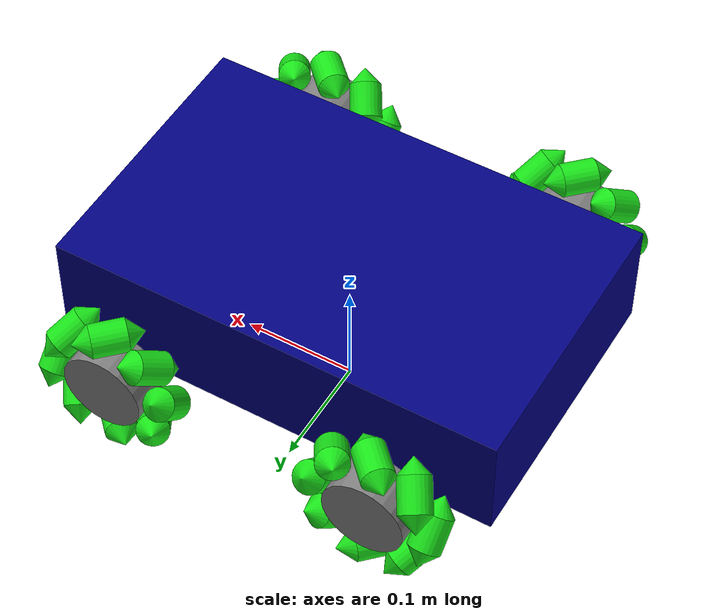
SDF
<?xml version="1.0"?>
<sdf version="1.10">
  <model name="bldc_car_mecanum">
    <static>false</static>
    <self_collide>false</self_collide>

    <link name="chassis">
      <pose>0 0 0.1 0 0 0</pose>
      <inertial>
        <mass>4.0</mass>
        <inertia>
          <ixx>0.0833333</ixx> <iyy>0.1666667</iyy> <izz>0.2166667</izz>
          <ixy>0</ixy> <ixz>0</ixz> <iyz>0</iyz>
        </inertia>
      </inertial>
      <collision name="chassis_collision">
        <pose>0 0 0.02 0 0 0</pose>
        <geometry><box><size>0.4 0.25 0.1</size></box></geometry>
      </collision>
      <visual name="chassis_visual">
        <pose>0 0 0.02 0 0 0</pose>
        <geometry><box><size>0.4 0.25 0.1</size></box></geometry>
        <material><ambient>0.0 0.0 0.5 1</ambient><diffuse>0.0 0.0 0.5 1</diffuse></material>
      </visual>
    </link>

    <link name="front_left_wheel">
      <pose relative_to="chassis">0.12 0.17 0 0 0 0</pose> <inertial>
        <mass>0.6</mass>
        <pose>0 0 0 1.5708 0 0</pose>
        <inertia><ixx>0.0027</ixx> <iyy>0.0027</iyy> <izz>0.005</izz></inertia>
      </inertial>
      <collision name="fl_collision">
        <pose>0 0 0 1.5708 0 0</pose>
        <geometry><cylinder><radius>0.036</radius><length>0.035</length></cylinder></geometry>
        <surface>
          <friction>
            <ode>
              <mu>2.5</mu>   <mu2>0.01</mu2>  <fdir1>0.7071 0.7071 0</fdir1> </ode>
          </friction>
        </surface>
      </collision>
      <visual name="fl_visual">
        <pose>0 0 0 1.5708 0 0</pose>
        <geometry><cylinder><radius>0.036</radius><length>0.035</length></cylinder></geometry>
        <material><ambient>0.5 0.5 0.5 1</ambient><diffuse>0.5 0.5 0.5 1</diffuse></material>
      </visual>
    </link>

    <link name="front_right_wheel">
      <pose relative_to="chassis">0.12 -0.17 0 0 0 0</pose> <inertial>
        <mass>1.0</mass>
        <pose>0 0 0 1.5708 0 0</pose>
        <inertia><ixx>0.0027</ixx> <iyy>0.0027</iyy> <izz>0.005</izz></inertia>
      </inertial>
      <collision name="fr_collision">
        <pose>0 0 0 1.5708 0 0</pose>
        <geometry><cylinder><radius>0.036</radius><length>0.035</length></cylinder></geometry>
        <surface>
          <friction>
            <ode>
              <mu>2.5</mu>   <mu2>0.01</mu2>  <fdir1>0.7071 -0.7071 0</fdir1> </ode>
          </friction>
        </surface>
      </collision>
      <visual name="fr_visual">
        <pose>0 0 0 1.5708 0 0</pose>
        <geometry><cylinder><radius>0.036</radius><length>0.035</length></cylinder></geometry>
        <material><ambient>0.5 0.5 0.5 1</ambient><diffuse>0.5 0.5 0.5 1</diffuse></material>
      </visual>
    </link>

    <link name="rear_left_wheel">
      <pose relative_to="chassis">-0.12 0.17 0 0 0 0</pose> <inertial>
        <mass>1.0</mass>
        <pose>0 0 0 1.5708 0 0</pose>
        <inertia><ixx>0.0027</ixx> <iyy>0.0027</iyy> <izz>0.005</izz></inertia>
      </inertial>
      <collision name="rl_collision">
        <pose>0 0 0 1.5708 0 0</pose>
        <geometry><cylinder><radius>0.036</radius><length>0.035</length></cylinder></geometry>
        <surface>
          <friction>
            <ode>
              <mu>2.5</mu>   <mu2>0.01</mu2>  <fdir1>0.7071 -0.7071 0</fdir1> </ode>
          </friction>
        </surface>
      </collision>
      <visual name="rl_visual">
        <pose>0 0 0 1.5708 0 0</pose>
        <geometry><cylinder><radius>0.036</radius><length>0.035</length></cylinder></geometry>
        <material><ambient>0.5 0.5 0.5 1</ambient><diffuse>0.5 0.5 0.5 1</diffuse></material>
      </visual>
    </link>

    <link name="rear_right_wheel">
      <pose relative_to="chassis">-0.12 -0.17 0 0 0 0</pose> <inertial>
        <mass>0.6</mass>
        <pose>0 0 0 1.5708 0 0</pose>
        <inertia><ixx>0.0027</ixx> <iyy>0.0027</iyy> <izz>0.005</izz></inertia>
      </inertial>
      <collision name="rr_collision">
        <pose>0 0 0 1.5708 0 0</pose>
        <geometry><cylinder><radius>0.036</radius><length>0.035</length></cylinder></geometry>
        <surface>
          <friction>
            <ode>
              <mu>2.5</mu>   <mu2>0.01</mu2>
              <fdir1>0.7071 0.7071 0</fdir1>
            </ode>
          </friction>
        </surface>
      </collision>
      <visual name="rr_visual">
        <pose>0 0 0 1.5708 0 0</pose>
        <geometry><cylinder><radius>0.036</radius><length>0.035</length></cylinder></geometry>
        <material><ambient>0.5 0.5 0.5 1</ambient><diffuse>0.5 0.5 0.5 1</diffuse></material>
      </visual>
    </link>

    <!-- ========== FL (front_left_wheel) ========== -->
    <link name="fl_roller_link_1">
      <pose relative_to="front_left_wheel">0 0 0.051 0 0 -0.7854</pose>
      <inertial>
        <mass>0.025</mass>
        <inertia><ixx>1e-5</ixx><iyy>1e-5</iyy><izz>2e-5</izz><ixy>0</ixy><ixz>0</ixz><iyz>0</iyz></inertia>
      </inertial>

      <collision name="fl_roller_collision_1">
        <pose>0 0 0 1.5708 0 0</pose>
        <geometry><cylinder><radius>0.014</radius><length>0.03</length></cylinder></geometry>
        <surface><friction><ode><mu>0.3</mu><mu2>0.3</mu2><slip1>0.0</slip1><slip2>0.0</slip2></ode></friction>
        <contact> <ode> <kp>5000.0</kp> <kd>60.0</kd> <max_vel>0.1</max_vel> <min_depth>0.01</min_depth></ode> </contact>
        </surface>
      </collision>

      <collision name="fl_roller_collision_1_cone1">
        <pose>0 0.0225 0 -1.5708 0 0</pose>
        <geometry><cone><radius>0.014</radius><length>0.015</length></cone></geometry>
        <surface><friction><ode><mu>0.3</mu><mu2>0.3</mu2><slip1>0.0</slip1><slip2>0.0</slip2></ode></friction>
        <contact> <ode> <kp>5000.0</kp> <kd>60.0</kd> <max_vel>0.1</max_vel> <min_depth>0.01</min_depth></ode> </contact>
        </surface>
      </collision>

      <collision name="fl_roller_collision_1_cone2">
        <pose>0 -0.0225 0 1.5708 0 0</pose>
        <geometry><cone><radius>0.014</radius><length>0.015</length></cone></geometry>
        <surface><friction><ode><mu>0.3</mu><mu2>0.3</mu2><slip1>0.0</slip1><slip2>0.0</slip2></ode></friction>
        <contact> <ode> <kp>5000.0</kp> <kd>60.0</kd> <max_vel>0.1</max_vel> <min_depth>0.01</min_depth></ode> </contact>
        </surface>
      </collision>

      <visual name="fl_roller_visual_1">
        <pose>0 0 0 1.5708 0 0</pose>
        <geometry><cylinder><radius>0.014</radius><length>0.03</length></cylinder></geometry>
        <material><ambient>0.1 0.8 0.1 1</ambient><diffuse>0.1 0.9 0.1 1</diffuse></material>
      </visual>

      <visual name="fl_roller_visual_1_cone1">
        <pose>0 0.0225 0 -1.5708 0 0</pose>
        <geometry><cone><radius>0.014</radius><length>0.015</length></cone></geometry>
        <material><ambient>0.1 0.8 0.1 1</ambient><diffuse>0.1 0.9 0.1 1</diffuse></material>
      </visual>

      <visual name="fl_roller_visual_1_cone2">
        <pose>0 -0.0225 0 1.5708 0 0</pose>
        <geometry><cone><radius>0.014</radius><length>0.015</length></cone></geometry>
        <material><ambient>0.1 0.8 0.1 1</ambient><diffuse>0.1 0.9 0.1 1</diffuse></material>
      </visual>
    </link>

    <joint name="fl_roller_joint_1" type="revolute">
      <parent>front_left_wheel</parent>
      <child>fl_roller_link_1</child>
      <axis><xyz>0 1 0</xyz><limit><lower>-1e16</lower><upper>1e16</upper></limit><dynamics><damping>0</damping></dynamics></axis>
      <physics><ode><implicit_spring_damper>1</implicit_spring_damper></ode></physics>
    </joint>

    <link name="fl_roller_link_2">
      <pose relative_to="front_left_wheel">0.03606 0 0.03606 -0.5557 0 -0.5557</pose>
      <inertial>
        <mass>0.025</mass>
        <inertia><ixx>1e-5</ixx><iyy>1e-5</iyy><izz>2e-5</izz><ixy>0</ixy><ixz>0</ixz><iyz>0</iyz></inertia>
      </inertial>

      <collision name="fl_roller_collision_2">
        <pose>0 0 0 1.5708 0 0</pose>
        <geometry><cylinder><radius>0.014</radius><length>0.03</length></cylinder></geometry>
        <surface><friction><ode><mu>0.3</mu><mu2>0.3</mu2><slip1>0.0</slip1><slip2>0.0</slip2></ode></friction>
        <contact> <ode> <kp>5000.0</kp> <kd>60.0</kd> <max_vel>0.1</max_vel> <min_depth>0.01</min_depth></ode> </contact>
        </surface>
      </collision>

      <collision name="fl_roller_collision_2_cone1">
        <pose>0 0.0225 0 -1.5708 0 0</pose>
        <geometry><cone><radius>0.014</radius><length>0.015</length></cone></geometry>
        <surface><friction><ode><mu>0.3</mu><mu2>0.3</mu2><slip1>0.0</slip1><slip2>0.0</slip2></ode></friction>
        <contact> <ode> <kp>5000.0</kp> <kd>60.0</kd> <max_vel>0.1</max_vel> <min_depth>0.01</min_depth></ode> </contact>
        </surface>
      </collision>

      <collision name="fl_roller_collision_2_cone2">
        <pose>0 -0.0225 0 1.5708 0 0</pose>
        <geometry><cone><radius>0.014</radius><length>0.015</length></cone></geometry>
        <surface><friction><ode><mu>0.3</mu><mu2>0.3</mu2><slip1>0.0</slip1><slip2>0.0</slip2></ode></friction>
        <contact> <ode> <kp>5000.0</kp> <kd>60.0</kd> <max_vel>0.1</max_vel> <min_depth>0.01</min_depth></ode> </contact>
        </surface>
      </collision>

      <visual name="fl_roller_visual_2">
        <pose>0 0 0 1.5708 0 0</pose>
        <geometry><cylinder><radius>0.014</radius><length>0.03</length></cylinder></geometry>
        <material><ambient>0.1 0.8 0.1 1</ambient><diffuse>0.1 0.9 0.1 1</diffuse></material>
      </visual>

      <visual name="fl_roller_visual_2_cone1">
        <pose>0 0.0225 0 -1.5708 0 0</pose>
        <geometry><cone><radius>0.014</radius><length>0.015</length></cone></geometry>
        <material><ambient>0.1 0.8 0.1 1</ambient><diffuse>0.1 0.9 0.1 1</diffuse></material>
      </visual>

      <visual name="fl_roller_visual_2_cone2">
        <pose>0 -0.0225 0 1.5708 0 0</pose>
        <geometry><cone><radius>0.014</radius><length>0.015</length></cone></geometry>
        <material><ambient>0.1 0.8 0.1 1</ambient><diffuse>0.1 0.9 0.1 1</diffuse></material>
      </visual>
    </link>

    <joint name="fl_roller_joint_2" type="revolute">
      <parent>front_left_wheel</parent>
      <child>fl_roller_link_2</child>
      <axis><xyz>0 1 0</xyz><limit><lower>-1e16</lower><upper>1e16</upper></limit><dynamics><damping>0</damping></dynamics></axis>
      <physics><ode><implicit_spring_damper>1</implicit_spring_damper></ode></physics>
    </joint>

    <link name="fl_roller_link_3">
      <pose relative_to="front_left_wheel">0.051 0 0 -0.7854 0 0</pose>
      <inertial>
        <mass>0.025</mass>
        <inertia><ixx>1e-5</ixx><iyy>1e-5</iyy><izz>2e-5</izz><ixy>0</ixy><ixz>0</ixz><iyz>0</iyz></inertia>
      </inertial>

      <collision name="fl_roller_collision_3">
        <pose>0 0 0 1.5708 0 0</pose>
        <geometry><cylinder><radius>0.014</radius><length>0.03</length></cylinder></geometry>
        <surface><friction><ode><mu>0.3</mu><mu2>0.3</mu2><slip1>0.0</slip1><slip2>0.0</slip2></ode></friction>
        <contact> <ode> <kp>5000.0</kp> <kd>60.0</kd> <max_vel>0.1</max_vel> <min_depth>0.01</min_depth></ode> </contact>
        </surface>
      </collision>

      <collision name="fl_roller_collision_3_cone1">
        <pose>0 0.0225 0 -1.5708 0 0</pose>
        <geometry><cone><radius>0.014</radius><length>0.015</length></cone></geometry>
        <surface><friction><ode><mu>0.3</mu><mu2>0.3</mu2><slip1>0.0</slip1><slip2>0.0</slip2></ode></friction>
        <contact> <ode> <kp>5000.0</kp> <kd>60.0</kd> <max_vel>0.1</max_vel> <min_depth>0.01</min_depth></ode> </contact>
        </surface>
      </collision>

      <collision name="fl_roller_collision_3_cone2">
        <pose>0 -0.0225 0 1.5708 0 0</pose>
        <geometry><cone><radius>0.014</radius><length>0.015</length></cone></geometry>
        <surface><friction><ode><mu>0.3</mu><mu2>0.3</mu2><slip1>0.0</slip1><slip2>0.0</slip2></ode></friction>
        <contact> <ode> <kp>5000.0</kp> <kd>60.0</kd> <max_vel>0.1</max_vel> <min_depth>0.01</min_depth></ode> </contact>
        </surface>
      </collision>

      <visual name="fl_roller_visual_3">
        <pose>0 0 0 1.5708 0 0</pose>
        <geometry><cylinder><radius>0.014</radius><length>0.03</length></cylinder></geometry>
        <material><ambient>0.1 0.8 0.1 1</ambient><diffuse>0.1 0.9 0.1 1</diffuse></material>
      </visual>

      <visual name="fl_roller_visual_3_cone1">
        <pose>0 0.0225 0 -1.5708 0 0</pose>
        <geometry><cone><radius>0.014</radius><length>0.015</length></cone></geometry>
        <material><ambient>0.1 0.8 0.1 1</ambient><diffuse>0.1 0.9 0.1 1</diffuse></material>
      </visual>

      <visual name="fl_roller_visual_3_cone2">
        <pose>0 -0.0225 0 1.5708 0 0</pose>
        <geometry><cone><radius>0.014</radius><length>0.015</length></cone></geometry>
        <material><ambient>0.1 0.8 0.1 1</ambient><diffuse>0.1 0.9 0.1 1</diffuse></material>
      </visual>
    </link>

    <joint name="fl_roller_joint_3" type="revolute">
      <parent>front_left_wheel</parent>
      <child>fl_roller_link_3</child>
      <axis><xyz>0 1 0</xyz><limit><lower>-1e16</lower><upper>1e16</upper></limit><dynamics><damping>0</damping></dynamics></axis>
      <physics><ode><implicit_spring_damper>1</implicit_spring_damper></ode></physics>
    </joint>

    <link name="fl_roller_link_4">
      <pose relative_to="front_left_wheel">0.03606 0 -0.03606 -0.5557 0 0.5557</pose>
      <inertial>
        <mass>0.025</mass>
        <inertia><ixx>1e-5</ixx><iyy>1e-5</iyy><izz>2e-5</izz><ixy>0</ixy><ixz>0</ixz><iyz>0</iyz></inertia>
      </inertial>

      <collision name="fl_roller_collision_4">
        <pose>0 0 0 1.5708 0 0</pose>
        <geometry><cylinder><radius>0.014</radius><length>0.03</length></cylinder></geometry>
        <surface><friction><ode><mu>0.3</mu><mu2>0.3</mu2><slip1>0.0</slip1><slip2>0.0</slip2></ode></friction>
        <contact> <ode> <kp>5000.0</kp> <kd>60.0</kd> <max_vel>0.1</max_vel> <min_depth>0.01</min_depth></ode> </contact>
        </surface>
      </collision>

      <collision name="fl_roller_collision_4_cone1">
        <pose>0 0.0225 0 -1.5708 0 0</pose>
        <geometry><cone><radius>0.014</radius><length>0.015</length></cone></geometry>
        <surface><friction><ode><mu>0.3</mu><mu2>0.3</mu2><slip1>0.0</slip1><slip2>0.0</slip2></ode></friction>
        <contact> <ode> <kp>5000.0</kp> <kd>60.0</kd> <max_vel>0.1</max_vel> <min_depth>0.01</min_depth></ode> </contact>
        </surface>
      </collision>

      <collision name="fl_roller_collision_4_cone2">
        <pose>0 -0.0225 0 1.5708 0 0</pose>
        <geometry><cone><radius>0.014</radius><length>0.015</length></cone></geometry>
        <surface><friction><ode><mu>0.3</mu><mu2>0.3</mu2><slip1>0.0</slip1><slip2>0.0</slip2></ode></friction>
        <contact> <ode> <kp>5000.0</kp> <kd>60.0</kd> <max_vel>0.1</max_vel> <min_depth>0.01</min_depth></ode> </contact>
        </surface>
      </collision>

      <visual name="fl_roller_visual_4">
        <pose>0 0 0 1.5708 0 0</pose>
        <geometry><cylinder><radius>0.014</radius><length>0.03</length></cylinder></geometry>
        <material><ambient>0.1 0.8 0.1 1</ambient><diffuse>0.1 0.9 0.1 1</diffuse></material>
      </visual>

      <visual name="fl_roller_visual_4_cone1">
        <pose>0 0.0225 0 -1.5708 0 0</pose>
        <geometry><cone><radius>0.014</radius><length>0.015</length></cone></geometry>
        <material><ambient>0.1 0.8 0.1 1</ambient><diffuse>0.1 0.9 0.1 1</diffuse></material>
      </visual>

      <visual name="fl_roller_visual_4_cone2">
        <pose>0 -0.0225 0 1.5708 0 0</pose>
        <geometry><cone><radius>0.014</radius><length>0.015</length></cone></geometry>
        <material><ambient>0.1 0.8 0.1 1</ambient><diffuse>0.1 0.9 0.1 1</diffuse></material>
      </visual>
    </link>

    <joint name="fl_roller_joint_4" type="revolute">
      <parent>front_left_wheel</parent>
      <child>fl_roller_link_4</child>
      <axis><xyz>0 1 0</xyz><limit><lower>-1e16</lower><upper>1e16</upper></limit><dynamics><damping>0</damping></dynamics></axis>
      <physics><ode><implicit_spring_damper>1</implicit_spring_damper></ode></physics>
    </joint>

    <link name="fl_roller_link_5">
      <pose relative_to="front_left_wheel">0 0 -0.051 0 0 0.7854</pose>
      <inertial>
        <mass>0.025</mass>
        <inertia><ixx>1e-5</ixx><iyy>1e-5</iyy><izz>2e-5</izz><ixy>0</ixy><ixz>0</ixz><iyz>0</iyz></inertia>
      </inertial>

      <collision name="fl_roller_collision_5">
        <pose>0 0 0 1.5708 0 0</pose>
        <geometry><cylinder><radius>0.014</radius><length>0.03</length></cylinder></geometry>
        <surface><friction><ode><mu>0.3</mu><mu2>0.3</mu2><slip1>0.0</slip1><slip2>0.0</slip2></ode></friction>
        <contact> <ode> <kp>5000.0</kp> <kd>60.0</kd> <max_vel>0.1</max_vel> <min_depth>0.01</min_depth></ode> </contact>
        </surface>
      </collision>

      <collision name="fl_roller_collision_5_cone1">
        <pose>0 0.0225 0 -1.5708 0 0</pose>
        <geometry><cone><radius>0.014</radius><length>0.015</length></cone></geometry>
        <surface><friction><ode><mu>0.3</mu><mu2>0.3</mu2><slip1>0.0</slip1><slip2>0.0</slip2></ode></friction>
        <contact> <ode> <kp>5000.0</kp> <kd>60.0</kd> <max_vel>0.1</max_vel> <min_depth>0.01</min_depth></ode> </contact>
        </surface>
      </collision>

      <collision name="fl_roller_collision_5_cone2">
        <pose>0 -0.0225 0 1.5708 0 0</pose>
        <geometry><cone><radius>0.014</radius><length>0.015</length></cone></geometry>
        <surface><friction><ode><mu>0.3</mu><mu2>0.3</mu2><slip1>0.0</slip1><slip2>0.0</slip2></ode></friction>
        <contact> <ode> <kp>5000.0</kp> <kd>60.0</kd> <max_vel>0.1</max_vel> <min_depth>0.01</min_depth></ode> </contact>
        </surface>
      </collision>

      <visual name="fl_roller_visual_5">
        <pose>0 0 0 1.5708 0 0</pose>
        <geometry><cylinder><radius>0.014</radius><length>0.03</length></cylinder></geometry>
        <material><ambient>0.1 0.8 0.1 1</ambient><diffuse>0.1 0.9 0.1 1</diffuse></material>
      </visual>

      <visual name="fl_roller_visual_5_cone1">
        <pose>0 0.0225 0 -1.5708 0 0</pose>
        <geometry><cone><radius>0.014</radius><length>0.015</length></cone></geometry>
        <material><ambient>0.1 0.8 0.1 1</ambient><diffuse>0.1 0.9 0.1 1</diffuse></material>
      </visual>

      <visual name="fl_roller_visual_5_cone2">
        <pose>0 -0.0225 0 1.5708 0 0</pose>
        <geometry><cone><radius>0.014</radius><length>0.015</length></cone></geometry>
        <material><ambient>0.1 0.8 0.1 1</ambient><diffuse>0.1 0.9 0.1 1</diffuse></material>
      </visual>
    </link>

    <joint name="fl_roller_joint_5" type="revolute">
      <parent>front_left_wheel</parent>
      <child>fl_roller_link_5</child>
      <axis><xyz>0 1 0</xyz><limit><lower>-1e16</lower><upper>1e16</upper></limit><dynamics><damping>0</damping></dynamics></axis>
      <physics><ode><implicit_spring_damper>1</implicit_spring_damper></ode></physics>
    </joint>

    <link name="fl_roller_link_6">
      <pose relative_to="front_left_wheel">-0.03606 0 -0.03606 0.5557 0 0.5557</pose>
      <inertial>
        <mass>0.025</mass>
        <inertia><ixx>1e-5</ixx><iyy>1e-5</iyy><izz>2e-5</izz><ixy>0</ixy><ixz>0</ixz><iyz>0</iyz></inertia>
      </inertial>

      <collision name="fl_roller_collision_6">
        <pose>0 0 0 1.5708 0 0</pose>
        <geometry><cylinder><radius>0.014</radius><length>0.03</length></cylinder></geometry>
        <surface><friction><ode><mu>0.3</mu><mu2>0.3</mu2><slip1>0.0</slip1><slip2>0.0</slip2></ode></friction>
        <contact> <ode> <kp>5000.0</kp> <kd>60.0</kd> <max_vel>0.1</max_vel> <min_depth>0.01</min_depth></ode> </contact>
        </surface>
      </collision>

      <collision name="fl_roller_collision_6_cone1">
        <pose>0 0.0225 0 -1.5708 0 0</pose>
        <geometry><cone><radius>0.014</radius><length>0.015</length></cone></geometry>
        <surface><friction><ode><mu>0.3</mu><mu2>0.3</mu2><slip1>0.0</slip1><slip2>0.0</slip2></ode></friction>
        <contact> <ode> <kp>5000.0</kp> <kd>60.0</kd> <max_vel>0.1</max_vel> <min_depth>0.01</min_depth></ode> </contact>
        </surface>
      </collision>

      <collision name="fl_roller_collision_6_cone2">
        <pose>0 -0.0225 0 1.5708 0 0</pose>
        <geometry><cone><radius>0.014</radius><length>0.015</length></cone></geometry>
        <surface><friction><ode><mu>0.3</mu><mu2>0.3</mu2><slip1>0.0</slip1><slip2>0.0</slip2></ode></friction>
        <contact> <ode> <kp>5000.0</kp> <kd>60.0</kd> <max_vel>0.1</max_vel> <min_depth>0.01</min_depth></ode> </contact>
        </surface>
      </collision>

      <visual name="fl_roller_visual_6">
        <pose>0 0 0 1.5708 0 0</pose>
        <geometry><cylinder><radius>0.014</radius><length>0.03</length></cylinder></geometry>
        <material><ambient>0.1 0.8 0.1 1</ambient><diffuse>0.1 0.9 0.1 1</diffuse></material>
      </visual>

      <visual name="fl_roller_visual_6_cone1">
        <pose>0 0.0225 0 -1.5708 0 0</pose>
        <geometry><cone><radius>0.014</radius><length>0.015</length></cone></geometry>
        <material><ambient>0.1 0.8 0.1 1</ambient><diffuse>0.1 0.9 0.1 1</diffuse></material>
      </visual>

      <visual name="fl_roller_visual_6_cone2">
        <pose>0 -0.0225 0 1.5708 0 0</pose>
        <geometry><cone><radius>0.014</radius><length>0.015</length></cone></geometry>
        <material><ambient>0.1 0.8 0.1 1</ambient><diffuse>0.1 0.9 0.1 1</diffuse></material>
      </visual>
    </link>

    <joint name="fl_roller_joint_6" type="revolute">
      <parent>front_left_wheel</parent>
      <child>fl_roller_link_6</child>
      <axis><xyz>0 1 0</xyz><limit><lower>-1e16</lower><upper>1e16</upper></limit><dynamics><damping>0</damping></dynamics></axis>
      <physics><ode><implicit_spring_damper>1</implicit_spring_damper></ode></physics>
    </joint>

    <link name="fl_roller_link_7">
      <pose relative_to="front_left_wheel">-0.051 0 0 0.7854 0 0</pose>
      <inertial>
        <mass>0.025</mass>
        <inertia><ixx>1e-5</ixx><iyy>1e-5</iyy><izz>2e-5</izz><ixy>0</ixy><ixz>0</ixz><iyz>0</iyz></inertia>
      </inertial>

      <collision name="fl_roller_collision_7">
        <pose>0 0 0 1.5708 0 0</pose>
        <geometry><cylinder><radius>0.014</radius><length>0.03</length></cylinder></geometry>
        <surface><friction><ode><mu>0.3</mu><mu2>0.3</mu2><slip1>0.0</slip1><slip2>0.0</slip2></ode></friction>
        <contact> <ode> <kp>5000.0</kp> <kd>60.0</kd> <max_vel>0.1</max_vel> <min_depth>0.01</min_depth></ode> </contact>
        </surface>
      </collision>

      <collision name="fl_roller_collision_7_cone1">
        <pose>0 0.0225 0 -1.5708 0 0</pose>
        <geometry><cone><radius>0.014</radius><length>0.015</length></cone></geometry>
        <surface><friction><ode><mu>0.3</mu><mu2>0.3</mu2><slip1>0.0</slip1><slip2>0.0</slip2></ode></friction>
        <contact> <ode> <kp>5000.0</kp> <kd>60.0</kd> <max_vel>0.1</max_vel> <min_depth>0.01</min_depth></ode> </contact>
        </surface>
      </collision>

      <collision name="fl_roller_collision_7_cone2">
        <pose>0 -0.0225 0 1.5708 0 0</pose>
        <geometry><cone><radius>0.014</radius><length>0.015</length></cone></geometry>
        <surface><friction><ode><mu>0.3</mu><mu2>0.3</mu2><slip1>0.0</slip1><slip2>0.0</slip2></ode></friction>
        <contact> <ode> <kp>5000.0</kp> <kd>60.0</kd> <max_vel>0.1</max_vel> <min_depth>0.01</min_depth></ode> </contact>
        </surface>
      </collision>

      <visual name="fl_roller_visual_7">
        <pose>0 0 0 1.5708 0 0</pose>
        <geometry><cylinder><radius>0.014</radius><length>0.03</length></cylinder></geometry>
        <material><ambient>0.1 0.8 0.1 1</ambient><diffuse>0.1 0.9 0.1 1</diffuse></material>
      </visual>

      <visual name="fl_roller_visual_7_cone1">
        <pose>0 0.0225 0 -1.5708 0 0</pose>
        <geometry><cone><radius>0.014</radius><length>0.015</length></cone></geometry>
        <material><ambient>0.1 0.8 0.1 1</ambient><diffuse>0.1 0.9 0.1 1</diffuse></material>
      </visual>

      <visual name="fl_roller_visual_7_cone2">
        <pose>0 -0.0225 0 1.5708 0 0</pose>
        <geometry><cone><radius>0.014</radius><length>0.015</length></cone></geometry>
        <material><ambient>0.1 0.8 0.1 1</ambient><diffuse>0.1 0.9 0.1 1</diffuse></material>
      </visual>
    </link>

    <joint name="fl_roller_joint_7" type="revolute">
      <parent>front_left_wheel</parent>
      <child>fl_roller_link_7</child>
      <axis><xyz>0 1 0</xyz><limit><lower>-1e16</lower><upper>1e16</upper></limit><dynamics><damping>0</damping></dynamics></axis>
      <physics><ode><implicit_spring_damper>1</implicit_spring_damper></ode></physics>
    </joint>

    <link name="fl_roller_link_8">
      <pose relative_to="front_left_wheel">-0.03606 0 0.03606 0.5557 0 -0.5557</pose>
      <inertial>
        <mass>0.025</mass>
        <inertia><ixx>1e-5</ixx><iyy>1e-5</iyy><izz>2e-5</izz><ixy>0</ixy><ixz>0</ixz><iyz>0</iyz></inertia>
      </inertial>

      <collision name="fl_roller_collision_8">
        <pose>0 0 0 1.5708 0 0</pose>
        <geometry><cylinder><radius>0.014</radius><length>0.03</length></cylinder></geometry>
        <surface><friction><ode><mu>0.3</mu><mu2>0.3</mu2><slip1>0.0</slip1><slip2>0.0</slip2></ode></friction>
        <contact> <ode> <kp>5000.0</kp> <kd>60.0</kd> <max_vel>0.1</max_vel> <min_depth>0.01</min_depth></ode> </contact>
        </surface>
      </collision>

      <collision name="fl_roller_collision_8_cone1">
        <pose>0 0.0225 0 -1.5708 0 0</pose>
        <geometry><cone><radius>0.014</radius><length>0.015</length></cone></geometry>
        <surface><friction><ode><mu>0.3</mu><mu2>0.3</mu2><slip1>0.0</slip1><slip2>0.0</slip2></ode></friction>
        <contact> <ode> <kp>5000.0</kp> <kd>60.0</kd> <max_vel>0.1</max_vel> <min_depth>0.01</min_depth></ode> </contact>
        </surface>
      </collision>

      <collision name="fl_roller_collision_8_cone2">
        <pose>0 -0.0225 0 1.5708 0 0</pose>
        <geometry><cone><radius>0.014</radius><length>0.015</length></cone></geometry>
        <surface><friction><ode><mu>0.3</mu><mu2>0.3</mu2><slip1>0.0</slip1><slip2>0.0</slip2></ode></friction>
        <contact> <ode> <kp>5000.0</kp> <kd>60.0</kd> <max_vel>0.1</max_vel> <min_depth>0.01</min_depth></ode> </contact>
        </surface>
      </collision>

      <visual name="fl_roller_visual_8">
        <pose>0 0 0 1.5708 0 0</pose>
        <geometry><cylinder><radius>0.014</radius><length>0.03</length></cylinder></geometry>
        <material><ambient>0.1 0.8 0.1 1</ambient><diffuse>0.1 0.9 0.1 1</diffuse></material>
      </visual>

      <visual name="fl_roller_visual_8_cone1">
        <pose>0 0.0225 0 -1.5708 0 0</pose>
        <geometry><cone><radius>0.014</radius><length>0.015</length></cone></geometry>
        <material><ambient>0.1 0.8 0.1 1</ambient><diffuse>0.1 0.9 0.1 1</diffuse></material>
      </visual>

      <visual name="fl_roller_visual_8_cone2">
        <pose>0 -0.0225 0 1.5708 0 0</pose>
        <geometry><cone><radius>0.014</radius><length>0.015</length></cone></geometry>
        <material><ambient>0.1 0.8 0.1 1</ambient><diffuse>0.1 0.9 0.1 1</diffuse></material>
      </visual>
    </link>

    <joint name="fl_roller_joint_8" type="revolute">
      <parent>front_left_wheel</parent>
      <child>fl_roller_link_8</child>
      <axis><xyz>0 1 0</xyz><limit><lower>-1e16</lower><upper>1e16</upper></limit><dynamics><damping>0</damping></dynamics></axis>
      <physics><ode><implicit_spring_damper>1</implicit_spring_damper></ode></physics>
    </joint>

    <!-- ========== FR (front_right_wheel) ========== -->
    <link name="fr_roller_link_1">
      <pose relative_to="front_right_wheel">0 0 0.051 0 0 0.7854</pose>
      <inertial>
        <mass>0.025</mass>
        <inertia><ixx>1e-5</ixx><iyy>1e-5</iyy><izz>2e-5</izz><ixy>0</ixy><ixz>0</ixz><iyz>0</iyz></inertia>
      </inertial>

      <collision name="fr_roller_collision_1">
        <pose>0 0 0 1.5708 0 0</pose>
        <geometry><cylinder><radius>0.014</radius><length>0.03</length></cylinder></geometry>
        <surface><friction><ode><mu>0.3</mu><mu2>0.3</mu2><slip1>0.0</slip1><slip2>0.0</slip2></ode></friction>
        <contact> <ode> <kp>5000.0</kp> <kd>60.0</kd> <max_vel>0.1</max_vel> <min_depth>0.01</min_depth></ode> </contact>
        </surface>
      </collision>
      <collision name="fr_roller_collision_1_cone1">
        <pose>0 0.0225 0 -1.5708 0 0</pose>
        <geometry><cone><radius>0.014</radius><length>0.015</length></cone></geometry>
        <surface><friction><ode><mu>0.3</mu><mu2>0.3</mu2><slip1>0.0</slip1><slip2>0.0</slip2></ode></friction>
        <contact> <ode> <kp>5000.0</kp> <kd>60.0</kd> <max_vel>0.1</max_vel> <min_depth>0.01</min_depth></ode> </contact>
        </surface>
      </collision>
      <collision name="fr_roller_collision_1_cone2">
        <pose>0 -0.0225 0 1.5708 0 0</pose>
        <geometry><cone><radius>0.014</radius><length>0.015</length></cone></geometry>
        <surface><friction><ode><mu>0.3</mu><mu2>0.3</mu2><slip1>0.0</slip1><slip2>0.0</slip2></ode></friction>
        <contact> <ode> <kp>5000.0</kp> <kd>60.0</kd> <max_vel>0.1</max_vel> <min_depth>0.01</min_depth></ode> </contact>
        </surface>
      </collision>

      <visual name="fr_roller_visual_1">
        <pose>0 0 0 1.5708 0 0</pose>
        <geometry><cylinder><radius>0.014</radius><length>0.03</length></cylinder></geometry>
        <material><ambient>0.1 0.8 0.1 1</ambient><diffuse>0.1 0.9 0.1 1</diffuse></material>
      </visual>
      <visual name="fr_roller_visual_1_cone1">
        <pose>0 0.0225 0 -1.5708 0 0</pose>
        <geometry><cone><radius>0.014</radius><length>0.015</length></cone></geometry>
        <material><ambient>0.1 0.8 0.1 1</ambient><diffuse>0.1 0.9 0.1 1</diffuse></material>
      </visual>
      <visual name="fr_roller_visual_1_cone2">
        <pose>0 -0.0225 0 1.5708 0 0</pose>
        <geometry><cone><radius>0.014</radius><length>0.015</length></cone></geometry>
        <material><ambient>0.1 0.8 0.1 1</ambient><diffuse>0.1 0.9 0.1 1</diffuse></material>
      </visual>
    </link>

    <joint name="fr_roller_joint_1" type="revolute">
      <parent>front_right_wheel</parent>
      <child>fr_roller_link_1</child>
      <axis><xyz>0 1 0</xyz><limit><lower>-1e16</lower><upper>1e16</upper></limit><dynamics><damping>0</damping></dynamics></axis>
      <physics><ode><implicit_spring_damper>1</implicit_spring_damper></ode></physics>
    </joint>

    <link name="fr_roller_link_2">
      <pose relative_to="front_right_wheel">0.03606 0 0.03606 0.5557 0 0.5557</pose>
      <inertial>
        <mass>0.025</mass>
        <inertia><ixx>1e-5</ixx><iyy>1e-5</iyy><izz>2e-5</izz><ixy>0</ixy><ixz>0</ixz><iyz>0</iyz></inertia>
      </inertial>

      <collision name="fr_roller_collision_2">
        <pose>0 0 0 1.5708 0 0</pose>
        <geometry><cylinder><radius>0.014</radius><length>0.03</length></cylinder></geometry>
        <surface><friction><ode><mu>0.3</mu><mu2>0.3</mu2><slip1>0.0</slip1><slip2>0.0</slip2></ode></friction>
        <contact> <ode> <kp>5000.0</kp> <kd>60.0</kd> <max_vel>0.1</max_vel> <min_depth>0.01</min_depth></ode> </contact>
        </surface>
      </collision>
      <collision name="fr_roller_collision_2_cone1">
        <pose>0 0.0225 0 -1.5708 0 0</pose>
        <geometry><cone><radius>0.014</radius><length>0.015</length></cone></geometry>
        <surface><friction><ode><mu>0.3</mu><mu2>0.3</mu2><slip1>0.0</slip1><slip2>0.0</slip2></ode></friction>
        <contact> <ode> <kp>5000.0</kp> <kd>60.0</kd> <max_vel>0.1</max_vel> <min_depth>0.01</min_depth></ode> </contact>
        </surface>
      </collision>
      <collision name="fr_roller_collision_2_cone2">
        <pose>0 -0.0225 0 1.5708 0 0</pose>
        <geometry><cone><radius>0.014</radius><length>0.015</length></cone></geometry>
        <surface><friction><ode><mu>0.3</mu><mu2>0.3</mu2><slip1>0.0</slip1><slip2>0.0</slip2></ode></friction>
        <contact> <ode> <kp>5000.0</kp> <kd>60.0</kd> <max_vel>0.1</max_vel> <min_depth>0.01</min_depth></ode> </contact>
        </surface>
      </collision>

      <visual name="fr_roller_visual_2">
        <pose>0 0 0 1.5708 0 0</pose>
        <geometry><cylinder><radius>0.014</radius><length>0.03</length></cylinder></geometry>
        <material><ambient>0.1 0.8 0.1 1</ambient><diffuse>0.1 0.9 0.1 1</diffuse></material>
      </visual>
      <visual name="fr_roller_visual_2_cone1">
        <pose>0 0.0225 0 -1.5708 0 0</pose>
        <geometry><cone><radius>0.014</radius><length>0.015</length></cone></geometry>
        <material><ambient>0.1 0.8 0.1 1</ambient><diffuse>0.1 0.9 0.1 1</diffuse></material>
      </visual>
      <visual name="fr_roller_visual_2_cone2">
        <pose>0 -0.0225 0 1.5708 0 0</pose>
        <geometry><cone><radius>0.014</radius><length>0.015</length></cone></geometry>
        <material><ambient>0.1 0.8 0.1 1</ambient><diffuse>0.1 0.9 0.1 1</diffuse></material>
      </visual>
    </link>

    <joint name="fr_roller_joint_2" type="revolute">
      <parent>front_right_wheel</parent>
      <child>fr_roller_link_2</child>
      <axis><xyz>0 1 0</xyz><limit><lower>-1e16</lower><upper>1e16</upper></limit><dynamics><damping>0</damping></dynamics></axis>
      <physics><ode><implicit_spring_damper>1</implicit_spring_damper></ode></physics>
    </joint>

    <link name="fr_roller_link_3">
      <pose relative_to="front_right_wheel">0.051 0 0 0.7854 0 0</pose>
      <inertial>
        <mass>0.025</mass>
        <inertia><ixx>1e-5</ixx><iyy>1e-5</iyy><izz>2e-5</izz><ixy>0</ixy><ixz>0</ixz><iyz>0</iyz></inertia>
      </inertial>

      <collision name="fr_roller_collision_3">
        <pose>0 0 0 1.5708 0 0</pose>
        <geometry><cylinder><radius>0.014</radius><length>0.03</length></cylinder></geometry>
        <surface><friction><ode><mu>0.3</mu><mu2>0.3</mu2><slip1>0.0</slip1><slip2>0.0</slip2></ode></friction>
        <contact> <ode> <kp>5000.0</kp> <kd>60.0</kd> <max_vel>0.1</max_vel> <min_depth>0.01</min_depth></ode> </contact>
        </surface>
      </collision>
      <collision name="fr_roller_collision_3_cone1">
        <pose>0 0.0225 0 -1.5708 0 0</pose>
        <geometry><cone><radius>0.014</radius><length>0.015</length></cone></geometry>
        <surface><friction><ode><mu>0.3</mu><mu2>0.3</mu2><slip1>0.0</slip1><slip2>0.0</slip2></ode></friction>
        <contact> <ode> <kp>5000.0</kp> <kd>60.0</kd> <max_vel>0.1</max_vel> <min_depth>0.01</min_depth></ode> </contact>
        </surface>
      </collision>
      <collision name="fr_roller_collision_3_cone2">
        <pose>0 -0.0225 0 1.5708 0 0</pose>
        <geometry><cone><radius>0.014</radius><length>0.015</length></cone></geometry>
        <surface><friction><ode><mu>0.3</mu><mu2>0.3</mu2><slip1>0.0</slip1><slip2>0.0</slip2></ode></friction>
        <contact> <ode> <kp>5000.0</kp> <kd>60.0</kd> <max_vel>0.1</max_vel> <min_depth>0.01</min_depth></ode> </contact>
        </surface>
      </collision>

      <visual name="fr_roller_visual_3">
        <pose>0 0 0 1.5708 0 0</pose>
        <geometry><cylinder><radius>0.014</radius><length>0.03</length></cylinder></geometry>
        <material><ambient>0.1 0.8 0.1 1</ambient><diffuse>0.1 0.9 0.1 1</diffuse></material>
      </visual>
      <visual name="fr_roller_visual_3_cone1">
        <pose>0 0.0225 0 -1.5708 0 0</pose>
        <geometry><cone><radius>0.014</radius><length>0.015</length></cone></geometry>
        <material><ambient>0.1 0.8 0.1 1</ambient><diffuse>0.1 0.9 0.1 1</diffuse></material>
      </visual>
      <visual name="fr_roller_visual_3_cone2">
        <pose>0 -0.0225 0 1.5708 0 0</pose>
        <geometry><cone><radius>0.014</radius><length>0.015</length></cone></geometry>
        <material><ambient>0.1 0.8 0.1 1</ambient><diffuse>0.1 0.9 0.1 1</diffuse></material>
      </visual>
    </link>

    <joint name="fr_roller_joint_3" type="revolute">
      <parent>front_right_wheel</parent>
      <child>fr_roller_link_3</child>
      <axis><xyz>0 1 0</xyz><limit><lower>-1e16</lower><upper>1e16</upper></limit><dynamics><damping>0</damping></dynamics></axis>
      <physics><ode><implicit_spring_damper>1</implicit_spring_damper></ode></physics>
    </joint>

    <link name="fr_roller_link_4">
      <pose relative_to="front_right_wheel">0.03606 0 -0.03606 0.5557 0 -0.5557</pose>
      <inertial>
        <mass>0.025</mass>
        <inertia><ixx>1e-5</ixx><iyy>1e-5</iyy><izz>2e-5</izz><ixy>0</ixy><ixz>0</ixz><iyz>0</iyz></inertia>
      </inertial>

      <collision name="fr_roller_collision_4">
        <pose>0 0 0 1.5708 0 0</pose>
        <geometry><cylinder><radius>0.014</radius><length>0.03</length></cylinder></geometry>
        <surface><friction><ode><mu>0.3</mu><mu2>0.3</mu2><slip1>0.0</slip1><slip2>0.0</slip2></ode></friction>
        <contact> <ode> <kp>5000.0</kp> <kd>60.0</kd> <max_vel>0.1</max_vel> <min_depth>0.01</min_depth></ode> </contact>
        </surface>
      </collision>
      <collision name="fr_roller_collision_4_cone1">
        <pose>0 0.0225 0 -1.5708 0 0</pose>
        <geometry><cone><radius>0.014</radius><length>0.015</length></cone></geometry>
        <surface><friction><ode><mu>0.3</mu><mu2>0.3</mu2><slip1>0.0</slip1><slip2>0.0</slip2></ode></friction>
        <contact> <ode> <kp>5000.0</kp> <kd>60.0</kd> <max_vel>0.1</max_vel> <min_depth>0.01</min_depth></ode> </contact>
        </surface>
      </collision>
      <collision name="fr_roller_collision_4_cone2">
        <pose>0 -0.0225 0 1.5708 0 0</pose>
        <geometry><cone><radius>0.014</radius><length>0.015</length></cone></geometry>
        <surface><friction><ode><mu>0.3</mu><mu2>0.3</mu2><slip1>0.0</slip1><slip2>0.0</slip2></ode></friction>
        <contact> <ode> <kp>5000.0</kp> <kd>60.0</kd> <max_vel>0.1</max_vel> <min_depth>0.01</min_depth></ode> </contact>
        </surface>
      </collision>

      <visual name="fr_roller_visual_4">
        <pose>0 0 0 1.5708 0 0</pose>
        <geometry><cylinder><radius>0.014</radius><length>0.03</length></cylinder></geometry>
        <material><ambient>0.1 0.8 0.1 1</ambient><diffuse>0.1 0.9 0.1 1</diffuse></material>
      </visual>
      <visual name="fr_roller_visual_4_cone1">
        <pose>0 0.0225 0 -1.5708 0 0</pose>
        <geometry><cone><radius>0.014</radius><length>0.015</length></cone></geometry>
        <material><ambient>0.1 0.8 0.1 1</ambient><diffuse>0.1 0.9 0.1 1</diffuse></material>
      </visual>
      <visual name="fr_roller_visual_4_cone2">
        <pose>0 -0.0225 0 1.5708 0 0</pose>
        <geometry><cone><radius>0.014</radius><length>0.015</length></cone></geometry>
        <material><ambient>0.1 0.8 0.1 1</ambient><diffuse>0.1 0.9 0.1 1</diffuse></material>
      </visual>
    </link>

    <joint name="fr_roller_joint_4" type="revolute">
      <parent>front_right_wheel</parent>
      <child>fr_roller_link_4</child>
      <axis><xyz>0 1 0</xyz><limit><lower>-1e16</lower><upper>1e16</upper></limit><dynamics><damping>0</damping></dynamics></axis>
      <physics><ode><implicit_spring_damper>1</implicit_spring_damper></ode></physics>
    </joint>

    <link name="fr_roller_link_5">
      <pose relative_to="front_right_wheel">0 0 -0.051 0 0 -0.7854</pose>
      <inertial>
        <mass>0.025</mass>
        <inertia><ixx>1e-5</ixx><iyy>1e-5</iyy><izz>2e-5</izz><ixy>0</ixy><ixz>0</ixz><iyz>0</iyz></inertia>
      </inertial>

      <collision name="fr_roller_collision_5">
        <pose>0 0 0 1.5708 0 0</pose>
        <geometry><cylinder><radius>0.014</radius><length>0.03</length></cylinder></geometry>
        <surface><friction><ode><mu>0.3</mu><mu2>0.3</mu2><slip1>0.0</slip1><slip2>0.0</slip2></ode></friction>
        <contact> <ode> <kp>5000.0</kp> <kd>60.0</kd> <max_vel>0.1</max_vel> <min_depth>0.01</min_depth></ode> </contact>
        </surface>
      </collision>
      <collision name="fr_roller_collision_5_cone1">
        <pose>0 0.0225 0 -1.5708 0 0</pose>
        <geometry><cone><radius>0.014</radius><length>0.015</length></cone></geometry>
        <surface><friction><ode><mu>0.3</mu><mu2>0.3</mu2><slip1>0.0</slip1><slip2>0.0</slip2></ode></friction>
        <contact> <ode> <kp>5000.0</kp> <kd>60.0</kd> <max_vel>0.1</max_vel> <min_depth>0.01</min_depth></ode> </contact>
        </surface>
      </collision>
      <collision name="fr_roller_collision_5_cone2">
        <pose>0 -0.0225 0 1.5708 0 0</pose>
        <geometry><cone><radius>0.014</radius><length>0.015</length></cone></geometry>
        <surface><friction><ode><mu>0.3</mu><mu2>0.3</mu2><slip1>0.0</slip1><slip2>0.0</slip2></ode></friction>
        <contact> <ode> <kp>5000.0</kp> <kd>60.0</kd> <max_vel>0.1</max_vel> <min_depth>0.01</min_depth></ode> </contact>
        </surface>
      </collision>

      <visual name="fr_roller_visual_5">
        <pose>0 0 0 1.5708 0 0</pose>
        <geometry><cylinder><radius>0.014</radius><length>0.03</length></cylinder></geometry>
        <material><ambient>0.1 0.8 0.1 1</ambient><diffuse>0.1 0.9 0.1 1</diffuse></material>
      </visual>
      <visual name="fr_roller_visual_5_cone1">
        <pose>0 0.0225 0 -1.5708 0 0</pose>
        <geometry><cone><radius>0.014</radius><length>0.015</length></cone></geometry>
        <material><ambient>0.1 0.8 0.1 1</ambient><diffuse>0.1 0.9 0.1 1</diffuse></material>
      </visual>
      <visual name="fr_roller_visual_5_cone2">
        <pose>0 -0.0225 0 1.5708 0 0</pose>
        <geometry><cone><radius>0.014</radius><length>0.015</length></cone></geometry>
        <material><ambient>0.1 0.8 0.1 1</ambient><diffuse>0.1 0.9 0.1 1</diffuse></material>
      </visual>
    </link>

    <joint name="fr_roller_joint_5" type="revolute">
      <parent>front_right_wheel</parent>
      <child>fr_roller_link_5</child>
      <axis><xyz>0 1 0</xyz><limit><lower>-1e16</lower><upper>1e16</upper></limit><dynamics><damping>0</damping></dynamics></axis>
      <physics><ode><implicit_spring_damper>1</implicit_spring_damper></ode></physics>
    </joint>

    <link name="fr_roller_link_6">
      <pose relative_to="front_right_wheel">-0.03606 0 -0.03606 -0.5557 0 -0.5557</pose>
      <inertial>
        <mass>0.025</mass>
        <inertia><ixx>1e-5</ixx><iyy>1e-5</iyy><izz>2e-5</izz><ixy>0</ixy><ixz>0</ixz><iyz>0</iyz></inertia>
      </inertial>

      <collision name="fr_roller_collision_6">
        <pose>0 0 0 1.5708 0 0</pose>
        <geometry><cylinder><radius>0.014</radius><length>0.03</length></cylinder></geometry>
        <surface><friction><ode><mu>0.3</mu><mu2>0.3</mu2><slip1>0.0</slip1><slip2>0.0</slip2></ode></friction>
        <contact> <ode> <kp>5000.0</kp> <kd>60.0</kd> <max_vel>0.1</max_vel> <min_depth>0.01</min_depth></ode> </contact>
        </surface>
      </collision>
      <collision name="fr_roller_collision_6_cone1">
        <pose>0 0.0225 0 -1.5708 0 0</pose>
        <geometry><cone><radius>0.014</radius><length>0.015</length></cone></geometry>
        <surface><friction><ode><mu>0.3</mu><mu2>0.3</mu2><slip1>0.0</slip1><slip2>0.0</slip2></ode></friction>
        <contact> <ode> <kp>5000.0</kp> <kd>60.0</kd> <max_vel>0.1</max_vel> <min_depth>0.01</min_depth></ode> </contact>
        </surface>
      </collision>
      <collision name="fr_roller_collision_6_cone2">
        <pose>0 -0.0225 0 1.5708 0 0</pose>
        <geometry><cone><radius>0.014</radius><length>0.015</length></cone></geometry>
        <surface><friction><ode><mu>0.3</mu><mu2>0.3</mu2><slip1>0.0</slip1><slip2>0.0</slip2></ode></friction>
        <contact> <ode> <kp>5000.0</kp> <kd>60.0</kd> <max_vel>0.1</max_vel> <min_depth>0.01</min_depth></ode> </contact>
        </surface>
      </collision>

      <visual name="fr_roller_visual_6">
        <pose>0 0 0 1.5708 0 0</pose>
        <geometry><cylinder><radius>0.014</radius><length>0.03</length></cylinder></geometry>
        <material><ambient>0.1 0.8 0.1 1</ambient><diffuse>0.1 0.9 0.1 1</diffuse></material>
      </visual>
      <visual name="fr_roller_visual_6_cone1">
        <pose>0 0.0225 0 -1.5708 0 0</pose>
        <geometry><cone><radius>0.014</radius><length>0.015</length></cone></geometry>
        <material><ambient>0.1 0.8 0.1 1</ambient><diffuse>0.1 0.9 0.1 1</diffuse></material>
      </visual>
      <visual name="fr_roller_visual_6_cone2">
        <pose>0 -0.0225 0 1.5708 0 0</pose>
        <geometry><cone><radius>0.014</radius><length>0.015</length></cone></geometry>
        <material><ambient>0.1 0.8 0.1 1</ambient><diffuse>0.1 0.9 0.1 1</diffuse></material>
      </visual>
    </link>

    <joint name="fr_roller_joint_6" type="revolute">
      <parent>front_right_wheel</parent>
      <child>fr_roller_link_6</child>
      <axis><xyz>0 1 0</xyz><limit><lower>-1e16</lower><upper>1e16</upper></limit><dynamics><damping>0</damping></dynamics></axis>
      <physics><ode><implicit_spring_damper>1</implicit_spring_damper></ode></physics>
    </joint>

    <link name="fr_roller_link_7">
      <pose relative_to="front_right_wheel">-0.051 0 0 -0.7854 0 0</pose>
      <inertial>
        <mass>0.025</mass>
        <inertia><ixx>1e-5</ixx><iyy>1e-5</iyy><izz>2e-5</izz><ixy>0</ixy><ixz>0</ixz><iyz>0</iyz></inertia>
      </inertial>

      <collision name="fr_roller_collision_7">
        <pose>0 0 0 1.5708 0 0</pose>
        <geometry><cylinder><radius>0.014</radius><length>0.03</length></cylinder></geometry>
        <surface><friction><ode><mu>0.3</mu><mu2>0.3</mu2><slip1>0.0</slip1><slip2>0.0</slip2></ode></friction>
        <contact> <ode> <kp>5000.0</kp> <kd>60.0</kd> <max_vel>0.1</max_vel> <min_depth>0.01</min_depth></ode> </contact>
        </surface>
      </collision>
      <collision name="fr_roller_collision_7_cone1">
        <pose>0 0.0225 0 -1.5708 0 0</pose>
        <geometry><cone><radius>0.014</radius><length>0.015</length></cone></geometry>
        <surface><friction><ode><mu>0.3</mu><mu2>0.3</mu2><slip1>0.0</slip1><slip2>0.0</slip2></ode></friction>
        <contact> <ode> <kp>5000.0</kp> <kd>60.0</kd> <max_vel>0.1</max_vel> <min_depth>0.01</min_depth></ode> </contact>
        </surface>
      </collision>
      <collision name="fr_roller_collision_7_cone2">
        <pose>0 -0.0225 0 1.5708 0 0</pose>
        <geometry><cone><radius>0.014</radius><length>0.015</length></cone></geometry>
        <surface><friction><ode><mu>0.3</mu><mu2>0.3</mu2><slip1>0.0</slip1><slip2>0.0</slip2></ode></friction>
        <contact> <ode> <kp>5000.0</kp> <kd>60.0</kd> <max_vel>0.1</max_vel> <min_depth>0.01</min_depth></ode> </contact>
        </surface>
      </collision>

      <visual name="fr_roller_visual_7">
        <pose>0 0 0 1.5708 0 0</pose>
        <geometry><cylinder><radius>0.014</radius><length>0.03</length></cylinder></geometry>
        <material><ambient>0.1 0.8 0.1 1</ambient><diffuse>0.1 0.9 0.1 1</diffuse></material>
      </visual>
      <visual name="fr_roller_visual_7_cone1">
        <pose>0 0.0225 0 -1.5708 0 0</pose>
        <geometry><cone><radius>0.014</radius><length>0.015</length></cone></geometry>
        <material><ambient>0.1 0.8 0.1 1</ambient><diffuse>0.1 0.9 0.1 1</diffuse></material>
      </visual>
      <visual name="fr_roller_visual_7_cone2">
        <pose>0 -0.0225 0 1.5708 0 0</pose>
        <geometry><cone><radius>0.014</radius><length>0.015</length></cone></geometry>
        <material><ambient>0.1 0.8 0.1 1</ambient><diffuse>0.1 0.9 0.1 1</diffuse></material>
      </visual>
    </link>

    <joint name="fr_roller_joint_7" type="revolute">
      <parent>front_right_wheel</parent>
      <child>fr_roller_link_7</child>
      <axis><xyz>0 1 0</xyz><limit><lower>-1e16</lower><upper>1e16</upper></limit><dynamics><damping>0</damping></dynamics></axis>
      <physics><ode><implicit_spring_damper>1</implicit_spring_damper></ode></physics>
    </joint>

    <link name="fr_roller_link_8">
      <pose relative_to="front_right_wheel">-0.03606 0 0.03606 -0.5557 0 0.5557</pose>
      <inertial>
        <mass>0.025</mass>
        <inertia><ixx>1e-5</ixx><iyy>1e-5</iyy><izz>2e-5</izz><ixy>0</ixy><ixz>0</ixz><iyz>0</iyz></inertia>
      </inertial>

      <collision name="fr_roller_collision_8">
        <pose>0 0 0 1.5708 0 0</pose>
        <geometry><cylinder><radius>0.014</radius><length>0.03</length></cylinder></geometry>
        <surface><friction><ode><mu>0.3</mu><mu2>0.3</mu2><slip1>0.0</slip1><slip2>0.0</slip2></ode></friction>
        <contact> <ode> <kp>5000.0</kp> <kd>60.0</kd> <max_vel>0.1</max_vel> <min_depth>0.01</min_depth></ode> </contact>
        </surface>
      </collision>
      <collision name="fr_roller_collision_8_cone1">
        <pose>0 0.0225 0 -1.5708 0 0</pose>
        <geometry><cone><radius>0.014</radius><length>0.015</length></cone></geometry>
        <surface><friction><ode><mu>0.3</mu><mu2>0.3</mu2><slip1>0.0</slip1><slip2>0.0</slip2></ode></friction>
        <contact> <ode> <kp>5000.0</kp> <kd>60.0</kd> <max_vel>0.1</max_vel> <min_depth>0.01</min_depth></ode> </contact>
        </surface>
      </collision>
      <collision name="fr_roller_collision_8_cone2">
        <pose>0 -0.0225 0 1.5708 0 0</pose>
        <geometry><cone><radius>0.014</radius><length>0.015</length></cone></geometry>
        <surface><friction><ode><mu>0.3</mu><mu2>0.3</mu2><slip1>0.0</slip1><slip2>0.0</slip2></ode></friction>
        <contact> <ode> <kp>5000.0</kp> <kd>60.0</kd> <max_vel>0.1</max_vel> <min_depth>0.01</min_depth></ode> </contact>
        </surface>
      </collision>

      <visual name="fr_roller_visual_8">
        <pose>0 0 0 1.5708 0 0</pose>
        <geometry><cylinder><radius>0.014</radius><length>0.03</length></cylinder></geometry>
        <material><ambient>0.1 0.8 0.1 1</ambient><diffuse>0.1 0.9 0.1 1</diffuse></material>
      </visual>
      <visual name="fr_roller_visual_8_cone1">
        <pose>0 0.0225 0 -1.5708 0 0</pose>
        <geometry><cone><radius>0.014</radius><length>0.015</length></cone></geometry>
        <material><ambient>0.1 0.8 0.1 1</ambient><diffuse>0.1 0.9 0.1 1</diffuse></material>
      </visual>
      <visual name="fr_roller_visual_8_cone2">
        <pose>0 -0.0225 0 1.5708 0 0</pose>
        <geometry><cone><radius>0.014</radius><length>0.015</length></cone></geometry>
        <material><ambient>0.1 0.8 0.1 1</ambient><diffuse>0.1 0.9 0.1 1</diffuse></material>
      </visual>
    </link>

    <joint name="fr_roller_joint_8" type="revolute">
      <parent>front_right_wheel</parent>
      <child>fr_roller_link_8</child>
      <axis><xyz>0 1 0</xyz><limit><lower>-1e16</lower><upper>1e16</upper></limit><dynamics><damping>0</damping></dynamics></axis>
      <physics><ode><implicit_spring_damper>1</implicit_spring_damper></ode></physics>
    </joint>

    <!-- ========== RL (rear_left_wheel) ========== -->
    <link name="rl_roller_link_1">
      <pose relative_to="rear_left_wheel">0 0 0.051 0 0 0.7854</pose>
      <inertial>
        <mass>0.025</mass>
        <inertia>
          <ixx>1e-5</ixx><iyy>1e-5</iyy><izz>2e-5</izz>
          <ixy>0</ixy><ixz>0</ixz><iyz>0</iyz>
        </inertia>
      </inertial>

      <collision name="rl_roller_collision_1">
        <pose>0 0 0 1.5708 0 0</pose>
        <geometry><cylinder><radius>0.014</radius><length>0.03</length></cylinder></geometry>
        <surface><friction><ode><mu>0.3</mu><mu2>0.3</mu2><slip1>0.0</slip1><slip2>0.0</slip2></ode></friction>
        <contact> <ode> <kp>5000.0</kp> <kd>60.0</kd> <max_vel>0.1</max_vel> <min_depth>0.01</min_depth></ode> </contact>
        </surface>
      </collision>
      <collision name="rl_roller_collision_1_cone1">
        <pose>0 0.0225 0 -1.5708 0 0</pose>
        <geometry><cone><radius>0.014</radius><length>0.015</length></cone></geometry>
        <surface><friction><ode><mu>0.3</mu><mu2>0.3</mu2><slip1>0.0</slip1><slip2>0.0</slip2></ode></friction>
        <contact> <ode> <kp>5000.0</kp> <kd>60.0</kd> <max_vel>0.1</max_vel> <min_depth>0.01</min_depth></ode> </contact>
        </surface>
      </collision>
      <collision name="rl_roller_collision_1_cone2">
        <pose>0 -0.0225 0 1.5708 0 0</pose>
        <geometry><cone><radius>0.014</radius><length>0.015</length></cone></geometry>
        <surface><friction><ode><mu>0.3</mu><mu2>0.3</mu2><slip1>0.0</slip1><slip2>0.0</slip2></ode></friction>
        <contact> <ode> <kp>5000.0</kp> <kd>60.0</kd> <max_vel>0.1</max_vel> <min_depth>0.01</min_depth></ode> </contact>
        </surface>
      </collision>

      <visual name="rl_roller_visual_1">
        <pose>0 0 0 1.5708 0 0</pose>
        <geometry><cylinder><radius>0.014</radius><length>0.03</length></cylinder></geometry>
        <material><ambient>0.1 0.8 0.1 1</ambient><diffuse>0.1 0.9 0.1 1</diffuse></material>
      </visual>
      <visual name="rl_roller_visual_1_cone1">
        <pose>0 0.0225 0 -1.5708 0 0</pose>
        <geometry><cone><radius>0.014</radius><length>0.015</length></cone></geometry>
        <material><ambient>0.1 0.8 0.1 1</ambient><diffuse>0.1 0.9 0.1 1</diffuse></material>
      </visual>
      <visual name="rl_roller_visual_1_cone2">
        <pose>0 -0.0225 0 1.5708 0 0</pose>
        <geometry><cone><radius>0.014</radius><length>0.015</length></cone></geometry>
        <material><ambient>0.1 0.8 0.1 1</ambient><diffuse>0.1 0.9 0.1 1</diffuse></material>
      </visual>
    </link>

    <joint name="rl_roller_joint_1" type="revolute">
      <parent>rear_left_wheel</parent>
      <child>rl_roller_link_1</child>
      <axis><xyz>0 1 0</xyz><limit><lower>-1e16</lower><upper>1e16</upper></limit><dynamics><damping>0</damping></dynamics></axis>
      <physics><ode><implicit_spring_damper>1</implicit_spring_damper></ode></physics>
    </joint>

    <link name="rl_roller_link_2">
      <pose relative_to="rear_left_wheel">0.03606 0 0.03606 0.5557 0 0.5557</pose>
      <inertial>
        <mass>0.025</mass>
        <inertia>
          <ixx>1e-5</ixx><iyy>1e-5</iyy><izz>2e-5</izz>
          <ixy>0</ixy><ixz>0</ixz><iyz>0</iyz>
        </inertia>
      </inertial>

      <collision name="rl_roller_collision_2">
        <pose>0 0 0 1.5708 0 0</pose>
        <geometry><cylinder><radius>0.014</radius><length>0.03</length></cylinder></geometry>
        <surface><friction><ode><mu>0.3</mu><mu2>0.3</mu2><slip1>0.0</slip1><slip2>0.0</slip2></ode></friction>
        <contact> <ode> <kp>5000.0</kp> <kd>60.0</kd> <max_vel>0.1</max_vel> <min_depth>0.01</min_depth></ode> </contact>
        </surface>
      </collision>
      <collision name="rl_roller_collision_2_cone1">
        <pose>0 0.0225 0 -1.5708 0 0</pose>
        <geometry><cone><radius>0.014</radius><length>0.015</length></cone></geometry>
        <surface><friction><ode><mu>0.3</mu><mu2>0.3</mu2><slip1>0.0</slip1><slip2>0.0</slip2></ode></friction>
        <contact> <ode> <kp>5000.0</kp> <kd>60.0</kd> <max_vel>0.1</max_vel> <min_depth>0.01</min_depth></ode> </contact>
        </surface>
      </collision>
      <collision name="rl_roller_collision_2_cone2">
        <pose>0 -0.0225 0 1.5708 0 0</pose>
        <geometry><cone><radius>0.014</radius><length>0.015</length></cone></geometry>
        <surface><friction><ode><mu>0.3</mu><mu2>0.3</mu2><slip1>0.0</slip1><slip2>0.0</slip2></ode></friction>
        <contact> <ode> <kp>5000.0</kp> <kd>60.0</kd> <max_vel>0.1</max_vel> <min_depth>0.01</min_depth></ode> </contact>
        </surface>
      </collision>

      <visual name="rl_roller_visual_2">
        <pose>0 0 0 1.5708 0 0</pose>
        <geometry><cylinder><radius>0.014</radius><length>0.03</length></cylinder></geometry>
        <material><ambient>0.1 0.8 0.1 1</ambient><diffuse>0.1 0.9 0.1 1</diffuse></material>
      </visual>
      <visual name="rl_roller_visual_2_cone1">
        <pose>0 0.0225 0 -1.5708 0 0</pose>
        <geometry><cone><radius>0.014</radius><length>0.015</length></cone></geometry>
        <material><ambient>0.1 0.8 0.1 1</ambient><diffuse>0.1 0.9 0.1 1</diffuse></material>
      </visual>
      <visual name="rl_roller_visual_2_cone2">
        <pose>0 -0.0225 0 1.5708 0 0</pose>
        <geometry><cone><radius>0.014</radius><length>0.015</length></cone></geometry>
        <material><ambient>0.1 0.8 0.1 1</ambient><diffuse>0.1 0.9 0.1 1</diffuse></material>
      </visual>
    </link>

    <joint name="rl_roller_joint_2" type="revolute">
      <parent>rear_left_wheel</parent>
      <child>rl_roller_link_2</child>
      <axis><xyz>0 1 0</xyz><limit><lower>-1e16</lower><upper>1e16</upper></limit><dynamics><damping>0</damping></dynamics></axis>
      <physics><ode><implicit_spring_damper>1</implicit_spring_damper></ode></physics>
    </joint>

    <link name="rl_roller_link_3">
      <pose relative_to="rear_left_wheel">0.051 0 0 0.7854 0 0</pose>
      <inertial>
        <mass>0.025</mass>
        <inertia>
          <ixx>1e-5</ixx><iyy>1e-5</iyy><izz>2e-5</izz>
          <ixy>0</ixy><ixz>0</ixz><iyz>0</iyz>
        </inertia>
      </inertial>

      <collision name="rl_roller_collision_3">
        <pose>0 0 0 1.5708 0 0</pose>
        <geometry><cylinder><radius>0.014</radius><length>0.03</length></cylinder></geometry>
        <surface><friction><ode><mu>0.3</mu><mu2>0.3</mu2><slip1>0.0</slip1><slip2>0.0</slip2></ode></friction>
        <contact> <ode> <kp>5000.0</kp> <kd>60.0</kd> <max_vel>0.1</max_vel> <min_depth>0.01</min_depth></ode> </contact>
        </surface>
      </collision>
      <collision name="rl_roller_collision_3_cone1">
        <pose>0 0.0225 0 -1.5708 0 0</pose>
        <geometry><cone><radius>0.014</radius><length>0.015</length></cone></geometry>
        <surface><friction><ode><mu>0.3</mu><mu2>0.3</mu2><slip1>0.0</slip1><slip2>0.0</slip2></ode></friction>
        <contact> <ode> <kp>5000.0</kp> <kd>60.0</kd> <max_vel>0.1</max_vel> <min_depth>0.01</min_depth></ode> </contact>
        </surface>
      </collision>
      <collision name="rl_roller_collision_3_cone2">
        <pose>0 -0.0225 0 1.5708 0 0</pose>
        <geometry><cone><radius>0.014</radius><length>0.015</length></cone></geometry>
        <surface><friction><ode><mu>0.3</mu><mu2>0.3</mu2><slip1>0.0</slip1><slip2>0.0</slip2></ode></friction>
        <contact> <ode> <kp>5000.0</kp> <kd>60.0</kd> <max_vel>0.1</max_vel> <min_depth>0.01</min_depth></ode> </contact>
        </surface>
      </collision>

      <visual name="rl_roller_visual_3">
        <pose>0 0 0 1.5708 0 0</pose>
        <geometry><cylinder><radius>0.014</radius><length>0.03</length></cylinder></geometry>
        <material><ambient>0.1 0.8 0.1 1</ambient><diffuse>0.1 0.9 0.1 1</diffuse></material>
      </visual>
      <visual name="rl_roller_visual_3_cone1">
        <pose>0 0.0225 0 -1.5708 0 0</pose>
        <geometry><cone><radius>0.014</radius><length>0.015</length></cone></geometry>
        <material><ambient>0.1 0.8 0.1 1</ambient><diffuse>0.1 0.9 0.1 1</diffuse></material>
      </visual>
      <visual name="rl_roller_visual_3_cone2">
        <pose>0 -0.0225 0 1.5708 0 0</pose>
        <geometry><cone><radius>0.014</radius><length>0.015</length></cone></geometry>
        <material><ambient>0.1 0.8 0.1 1</ambient><diffuse>0.1 0.9 0.1 1</diffuse></material>
      </visual>
    </link>

    <joint name="rl_roller_joint_3" type="revolute">
      <parent>rear_left_wheel</parent>
      <child>rl_roller_link_3</child>
      <axis><xyz>0 1 0</xyz><limit><lower>-1e16</lower><upper>1e16</upper></limit><dynamics><damping>0</damping></dynamics></axis>
      <physics><ode><implicit_spring_damper>1</implicit_spring_damper></ode></physics>
    </joint>

    <link name="rl_roller_link_4">
      <pose relative_to="rear_left_wheel">0.03606 0 -0.03606 0.5557 0 -0.5557</pose>
      <inertial>
        <mass>0.025</mass>
        <inertia>
          <ixx>1e-5</ixx><iyy>1e-5</iyy><izz>2e-5</izz>
          <ixy>0</ixy><ixz>0</ixz><iyz>0</iyz>
        </inertia>
      </inertial>

      <collision name="rl_roller_collision_4">
        <pose>0 0 0 1.5708 0 0</pose>
        <geometry><cylinder><radius>0.014</radius><length>0.03</length></cylinder></geometry>
        <surface><friction><ode><mu>0.3</mu><mu2>0.3</mu2><slip1>0.0</slip1><slip2>0.0</slip2></ode></friction>
        <contact> <ode> <kp>5000.0</kp> <kd>60.0</kd> <max_vel>0.1</max_vel> <min_depth>0.01</min_depth></ode> </contact>
        </surface>
      </collision>
      <collision name="rl_roller_collision_4_cone1">
        <pose>0 0.0225 0 -1.5708 0 0</pose>
        <geometry><cone><radius>0.014</radius><length>0.015</length></cone></geometry>
        <surface><friction><ode><mu>0.3</mu><mu2>0.3</mu2><slip1>0.0</slip1><slip2>0.0</slip2></ode></friction>
        <contact> <ode> <kp>5000.0</kp> <kd>60.0</kd> <max_vel>0.1</max_vel> <min_depth>0.01</min_depth></ode> </contact>
        </surface>
      </collision>
      <collision name="rl_roller_collision_4_cone2">
        <pose>0 -0.0225 0 1.5708 0 0</pose>
        <geometry><cone><radius>0.014</radius><length>0.015</length></cone></geometry>
        <surface><friction><ode><mu>0.3</mu><mu2>0.3</mu2><slip1>0.0</slip1><slip2>0.0</slip2></ode></friction>
        <contact> <ode> <kp>5000.0</kp> <kd>60.0</kd> <max_vel>0.1</max_vel> <min_depth>0.01</min_depth></ode> </contact>
        </surface>
      </collision>

      <visual name="rl_roller_visual_4">
        <pose>0 0 0 1.5708 0 0</pose>
        <geometry><cylinder><radius>0.014</radius><length>0.03</length></cylinder></geometry>
        <material><ambient>0.1 0.8 0.1 1</ambient><diffuse>0.1 0.9 0.1 1</diffuse></material>
      </visual>
      <visual name="rl_roller_visual_4_cone1">
        <pose>0 0.0225 0 -1.5708 0 0</pose>
        <geometry><cone><radius>0.014</radius><length>0.015</length></cone></geometry>
        <material><ambient>0.1 0.8 0.1 1</ambient><diffuse>0.1 0.9 0.1 1</diffuse></material>
      </visual>
      <visual name="rl_roller_visual_4_cone2">
        <pose>0 -0.0225 0 1.5708 0 0</pose>
        <geometry><cone><radius>0.014</radius><length>0.015</length></cone></geometry>
        <material><ambient>0.1 0.8 0.1 1</ambient><diffuse>0.1 0.9 0.1 1</diffuse></material>
      </visual>
    </link>

    <joint name="rl_roller_joint_4" type="revolute">
      <parent>rear_left_wheel</parent>
      <child>rl_roller_link_4</child>
      <axis><xyz>0 1 0</xyz><limit><lower>-1e16</lower><upper>1e16</upper></limit><dynamics><damping>0</damping></dynamics></axis>
      <physics><ode><implicit_spring_damper>1</implicit_spring_damper></ode></physics>
    </joint>

    <link name="rl_roller_link_5">
      <pose relative_to="rear_left_wheel">0 0 -0.051 0 0 -0.7854</pose>
      <inertial>
        <mass>0.025</mass>
        <inertia>
          <ixx>1e-5</ixx><iyy>1e-5</iyy><izz>2e-5</izz>
          <ixy>0</ixy><ixz>0</ixz><iyz>0</iyz>
        </inertia>
      </inertial>

      <collision name="rl_roller_collision_5">
        <pose>0 0 0 1.5708 0 0</pose>
        <geometry><cylinder><radius>0.014</radius><length>0.03</length></cylinder></geometry>
        <surface><friction><ode><mu>0.3</mu><mu2>0.3</mu2><slip1>0.0</slip1><slip2>0.0</slip2></ode></friction>
        <contact> <ode> <kp>5000.0</kp> <kd>60.0</kd> <max_vel>0.1</max_vel> <min_depth>0.01</min_depth></ode> </contact>
        </surface>
      </collision>
      <collision name="rl_roller_collision_5_cone1">
        <pose>0 0.0225 0 -1.5708 0 0</pose>
        <geometry><cone><radius>0.014</radius><length>0.015</length></cone></geometry>
        <surface><friction><ode><mu>0.3</mu><mu2>0.3</mu2><slip1>0.0</slip1><slip2>0.0</slip2></ode></friction>
        <contact> <ode> <kp>5000.0</kp> <kd>60.0</kd> <max_vel>0.1</max_vel> <min_depth>0.01</min_depth></ode> </contact>
        </surface>
      </collision>
      <collision name="rl_roller_collision_5_cone2">
        <pose>0 -0.0225 0 1.5708 0 0</pose>
        <geometry><cone><radius>0.014</radius><length>0.015</length></cone></geometry>
        <surface><friction><ode><mu>0.3</mu><mu2>0.3</mu2><slip1>0.0</slip1><slip2>0.0</slip2></ode></friction>
        <contact> <ode> <kp>5000.0</kp> <kd>60.0</kd> <max_vel>0.1</max_vel> <min_depth>0.01</min_depth></ode> </contact>
        </surface>
      </collision>

      <visual name="rl_roller_visual_5">
        <pose>0 0 0 1.5708 0 0</pose>
        <geometry><cylinder><radius>0.014</radius><length>0.03</length></cylinder></geometry>
        <material><ambient>0.1 0.8 0.1 1</ambient><diffuse>0.1 0.9 0.1 1</diffuse></material>
      </visual>
      <visual name="rl_roller_visual_5_cone1">
        <pose>0 0.0225 0 -1.5708 0 0</pose>
        <geometry><cone><radius>0.014</radius><length>0.015</length></cone></geometry>
        <material><ambient>0.1 0.8 0.1 1</ambient><diffuse>0.1 0.9 0.1 1</diffuse></material>
      </visual>
      <visual name="rl_roller_visual_5_cone2">
        <pose>0 -0.0225 0 1.5708 0 0</pose>
        <geometry><cone><radius>0.014</radius><length>0.015</length></cone></geometry>
        <material><ambient>0.1 0.8 0.1 1</ambient><diffuse>0.1 0.9 0.1 1</diffuse></material>
      </visual>
    </link>

    <joint name="rl_roller_joint_5" type="revolute">
      <parent>rear_left_wheel</parent>
      <child>rl_roller_link_5</child>
      <axis><xyz>0 1 0</xyz><limit><lower>-1e16</lower><upper>1e16</upper></limit><dynamics><damping>0</damping></dynamics></axis>
      <physics><ode><implicit_spring_damper>1</implicit_spring_damper></ode></physics>
    </joint>

    <link name="rl_roller_link_6">
      <pose relative_to="rear_left_wheel">-0.03606 0 -0.03606 -0.5557 0 -0.5557</pose>
      <inertial>
        <mass>0.025</mass>
        <inertia>
          <ixx>1e-5</ixx><iyy>1e-5</iyy><izz>2e-5</izz>
          <ixy>0</ixy><ixz>0</ixz><iyz>0</iyz>
        </inertia>
      </inertial>

      <collision name="rl_roller_collision_6">
        <pose>0 0 0 1.5708 0 0</pose>
        <geometry><cylinder><radius>0.014</radius><length>0.03</length></cylinder></geometry>
        <surface><friction><ode><mu>0.3</mu><mu2>0.3</mu2><slip1>0.0</slip1><slip2>0.0</slip2></ode></friction>
        <contact> <ode> <kp>5000.0</kp> <kd>60.0</kd> <max_vel>0.1</max_vel> <min_depth>0.01</min_depth></ode> </contact>
        </surface>
      </collision>
      <collision name="rl_roller_collision_6_cone1">
        <pose>0 0.0225 0 -1.5708 0 0</pose>
        <geometry><cone><radius>0.014</radius><length>0.015</length></cone></geometry>
        <surface><friction><ode><mu>0.3</mu><mu2>0.3</mu2><slip1>0.0</slip1><slip2>0.0</slip2></ode></friction>
        <contact> <ode> <kp>5000.0</kp> <kd>60.0</kd> <max_vel>0.1</max_vel> <min_depth>0.01</min_depth></ode> </contact>
        </surface>
      </collision>
      <collision name="rl_roller_collision_6_cone2">
        <pose>0 -0.0225 0 1.5708 0 0</pose>
        <geometry><cone><radius>0.014</radius><length>0.015</length></cone></geometry>
        <surface><friction><ode><mu>0.3</mu><mu2>0.3</mu2><slip1>0.0</slip1><slip2>0.0</slip2></ode></friction>
        <contact> <ode> <kp>5000.0</kp> <kd>60.0</kd> <max_vel>0.1</max_vel> <min_depth>0.01</min_depth></ode> </contact>
        </surface>
      </collision>

      <visual name="rl_roller_visual_6">
        <pose>0 0 0 1.5708 0 0</pose>
        <geometry><cylinder><radius>0.014</radius><length>0.03</length></cylinder></geometry>
        <material><ambient>0.1 0.8 0.1 1</ambient><diffuse>0.1 0.9 0.1 1</diffuse></material>
      </visual>
      <visual name="rl_roller_visual_6_cone1">
        <pose>0 0.0225 0 -1.5708 0 0</pose>
        <geometry><cone><radius>0.014</radius><length>0.015</length></cone></geometry>
        <material><ambient>0.1 0.8 0.1 1</ambient><diffuse>0.1 0.9 0.1 1</diffuse></material>
      </visual>
      <visual name="rl_roller_visual_6_cone2">
        <pose>0 -0.0225 0 1.5708 0 0</pose>
        <geometry><cone><radius>0.014</radius><length>0.015</length></cone></geometry>
        <material><ambient>0.1 0.8 0.1 1</ambient><diffuse>0.1 0.9 0.1 1</diffuse></material>
      </visual>
    </link>

    <joint name="rl_roller_joint_6" type="revolute">
      <parent>rear_left_wheel</parent>
      <child>rl_roller_link_6</child>
      <axis><xyz>0 1 0</xyz><limit><lower>-1e16</lower><upper>1e16</upper></limit><dynamics><damping>0</damping></dynamics></axis>
      <physics><ode><implicit_spring_damper>1</implicit_spring_damper></ode></physics>
    </joint>

    <link name="rl_roller_link_7">
      <pose relative_to="rear_left_wheel">-0.051 0 0 -0.7854 0 0</pose>
      <inertial>
        <mass>0.025</mass>
        <inertia>
          <ixx>1e-5</ixx><iyy>1e-5</iyy><izz>2e-5</izz>
          <ixy>0</ixy><ixz>0</ixz><iyz>0</iyz>
        </inertia>
      </inertial>

      <collision name="rl_roller_collision_7">
        <pose>0 0 0 1.5708 0 0</pose>
        <geometry><cylinder><radius>0.014</radius><length>0.03</length></cylinder></geometry>
        <surface><friction><ode><mu>0.3</mu><mu2>0.3</mu2><slip1>0.0</slip1><slip2>0.0</slip2></ode></friction>
        <contact> <ode> <kp>5000.0</kp> <kd>60.0</kd> <max_vel>0.1</max_vel> <min_depth>0.01</min_depth></ode> </contact>
        </surface>
      </collision>
      <collision name="rl_roller_collision_7_cone1">
        <pose>0 0.0225 0 -1.5708 0 0</pose>
        <geometry><cone><radius>0.014</radius><length>0.015</length></cone></geometry>
        <surface><friction><ode><mu>0.3</mu><mu2>0.3</mu2><slip1>0.0</slip1><slip2>0.0</slip2></ode></friction>
        <contact> <ode> <kp>5000.0</kp> <kd>60.0</kd> <max_vel>0.1</max_vel> <min_depth>0.01</min_depth></ode> </contact>
        </surface>
      </collision>
      <collision name="rl_roller_collision_7_cone2">
        <pose>0 -0.0225 0 1.5708 0 0</pose>
        <geometry><cone><radius>0.014</radius><length>0.015</length></cone></geometry>
        <surface><friction><ode><mu>0.3</mu><mu2>0.3</mu2><slip1>0.0</slip1><slip2>0.0</slip2></ode></friction>
        <contact> <ode> <kp>5000.0</kp> <kd>60.0</kd> <max_vel>0.1</max_vel> <min_depth>0.01</min_depth></ode> </contact>
        </surface>
      </collision>

      <visual name="rl_roller_visual_7">
        <pose>0 0 0 1.5708 0 0</pose>
        <geometry><cylinder><radius>0.014</radius><length>0.03</length></cylinder></geometry>
        <material><ambient>0.1 0.8 0.1 1</ambient><diffuse>0.1 0.9 0.1 1</diffuse></material>
      </visual>
      <visual name="rl_roller_visual_7_cone1">
        <pose>0 0.0225 0 -1.5708 0 0</pose>
        <geometry><cone><radius>0.014</radius><length>0.015</length></cone></geometry>
        <material><ambient>0.1 0.8 0.1 1</ambient><diffuse>0.1 0.9 0.1 1</diffuse></material>
      </visual>
      <visual name="rl_roller_visual_7_cone2">
        <pose>0 -0.0225 0 1.5708 0 0</pose>
        <geometry><cone><radius>0.014</radius><length>0.015</length></cone></geometry>
        <material><ambient>0.1 0.8 0.1 1</ambient><diffuse>0.1 0.9 0.1 1</diffuse></material>
      </visual>
    </link>

    <joint name="rl_roller_joint_7" type="revolute">
      <parent>rear_left_wheel</parent>
      <child>rl_roller_link_7</child>
      <axis><xyz>0 1 0</xyz><limit><lower>-1e16</lower><upper>1e16</upper></limit><dynamics><damping>0</damping></dynamics></axis>
      <physics><ode><implicit_spring_damper>1</implicit_spring_damper></ode></physics>
    </joint>

    <link name="rl_roller_link_8">
      <pose relative_to="rear_left_wheel">-0.03606 0 0.03606 -0.5557 0 0.5557</pose>
      <inertial>
        <mass>0.025</mass>
        <inertia>
          <ixx>1e-5</ixx><iyy>1e-5</iyy><izz>2e-5</izz>
          <ixy>0</ixy><ixz>0</ixz><iyz>0</iyz>
        </inertia>
      </inertial>

      <collision name="rl_roller_collision_8">
        <pose>0 0 0 1.5708 0 0</pose>
        <geometry><cylinder><radius>0.014</radius><length>0.03</length></cylinder></geometry>
        <surface><friction><ode><mu>0.3</mu><mu2>0.3</mu2><slip1>0.0</slip1><slip2>0.0</slip2></ode></friction>
        <contact> <ode> <kp>5000.0</kp> <kd>60.0</kd> <max_vel>0.1</max_vel> <min_depth>0.01</min_depth></ode> </contact>
        </surface>
      </collision>
      <collision name="rl_roller_collision_8_cone1">
        <pose>0 0.0225 0 -1.5708 0 0</pose>
        <geometry><cone><radius>0.014</radius><length>0.015</length></cone></geometry>
        <surface><friction><ode><mu>0.3</mu><mu2>0.3</mu2><slip1>0.0</slip1><slip2>0.0</slip2></ode></friction>
        <contact> <ode> <kp>5000.0</kp> <kd>60.0</kd> <max_vel>0.1</max_vel> <min_depth>0.01</min_depth></ode> </contact>
        </surface>
      </collision>
      <collision name="rl_roller_collision_8_cone2">
        <pose>0 -0.0225 0 1.5708 0 0</pose>
        <geometry><cone><radius>0.014</radius><length>0.015</length></cone></geometry>
        <surface><friction><ode><mu>0.3</mu><mu2>0.3</mu2><slip1>0.0</slip1><slip2>0.0</slip2></ode></friction>
        <contact> <ode> <kp>5000.0</kp> <kd>60.0</kd> <max_vel>0.1</max_vel> <min_depth>0.01</min_depth></ode> </contact>
        </surface>
      </collision>

      <visual name="rl_roller_visual_8">
        <pose>0 0 0 1.5708 0 0</pose>
        <geometry><cylinder><radius>0.014</radius><length>0.03</length></cylinder></geometry>
        <material><ambient>0.1 0.8 0.1 1</ambient><diffuse>0.1 0.9 0.1 1</diffuse></material>
      </visual>
      <visual name="rl_roller_visual_8_cone1">
        <pose>0 0.0225 0 -1.5708 0 0</pose>
        <geometry><cone><radius>0.014</radius><length>0.015</length></cone></geometry>
        <material><ambient>0.1 0.8 0.1 1</ambient><diffuse>0.1 0.9 0.1 1</diffuse></material>
      </visual>
      <visual name="rl_roller_visual_8_cone2">
        <pose>0 -0.0225 0 1.5708 0 0</pose>
        <geometry><cone><radius>0.014</radius><length>0.015</length></cone></geometry>
        <material><ambient>0.1 0.8 0.1 1</ambient><diffuse>0.1 0.9 0.1 1</diffuse></material>
      </visual>
    </link>

    <joint name="rl_roller_joint_8" type="revolute">
      <parent>rear_left_wheel</parent>
      <child>rl_roller_link_8</child>
      <axis><xyz>0 1 0</xyz><limit><lower>-1e16</lower><upper>1e16</upper></limit><dynamics><damping>0</damping></dynamics></axis>
      <physics><ode><implicit_spring_damper>1</implicit_spring_damper></ode></physics>
    </joint>

    <!-- ========== RR (rear_right_wheel) ========== -->
    <link name="rr_roller_link_1">
      <pose relative_to="rear_right_wheel">0 0 0.051 0 0 -0.7854</pose>
      <inertial>
        <mass>0.025</mass>
        <inertia>
          <ixx>1e-5</ixx><iyy>1e-5</iyy><izz>2e-5</izz>
          <ixy>0</ixy><ixz>0</ixz><iyz>0</iyz>
        </inertia>
      </inertial>

      <collision name="rr_roller_collision_1">
        <pose>0 0 0 1.5708 0 0</pose>
        <geometry><cylinder><radius>0.014</radius><length>0.03</length></cylinder></geometry>
        <surface><friction><ode><mu>0.3</mu><mu2>0.3</mu2><slip1>0.0</slip1><slip2>0.0</slip2></ode></friction>
        <contact> <ode> <kp>5000.0</kp> <kd>60.0</kd> <max_vel>0.1</max_vel> <min_depth>0.01</min_depth></ode> </contact>
        </surface>
      </collision>
      <collision name="rr_roller_collision_1_cone1">
        <pose>0 0.0225 0 -1.5708 0 0</pose>
        <geometry><cone><radius>0.014</radius><length>0.015</length></cone></geometry>
        <surface><friction><ode><mu>0.3</mu><mu2>0.3</mu2><slip1>0.0</slip1><slip2>0.0</slip2></ode></friction>
        <contact> <ode> <kp>5000.0</kp> <kd>60.0</kd> <max_vel>0.1</max_vel> <min_depth>0.01</min_depth></ode> </contact>
        </surface>
      </collision>
      <collision name="rr_roller_collision_1_cone2">
        <pose>0 -0.0225 0 1.5708 0 0</pose>
        <geometry><cone><radius>0.014</radius><length>0.015</length></cone></geometry>
        <surface><friction><ode><mu>0.3</mu><mu2>0.3</mu2><slip1>0.0</slip1><slip2>0.0</slip2></ode></friction>
        <contact> <ode> <kp>5000.0</kp> <kd>60.0</kd> <max_vel>0.1</max_vel> <min_depth>0.01</min_depth></ode> </contact>
        </surface>
      </collision>

      <visual name="rr_roller_visual_1">
        <pose>0 0 0 1.5708 0 0</pose>
        <geometry><cylinder><radius>0.014</radius><length>0.03</length></cylinder></geometry>
        <material><ambient>0.1 0.8 0.1 1</ambient><diffuse>0.1 0.9 0.1 1</diffuse></material>
      </visual>
      <visual name="rr_roller_visual_1_cone1">
        <pose>0 0.0225 0 -1.5708 0 0</pose>
        <geometry><cone><radius>0.014</radius><length>0.015</length></cone></geometry>
        <material><ambient>0.1 0.8 0.1 1</ambient><diffuse>0.1 0.9 0.1 1</diffuse></material>
      </visual>
      <visual name="rr_roller_visual_1_cone2">
        <pose>0 -0.0225 0 1.5708 0 0</pose>
        <geometry><cone><radius>0.014</radius><length>0.015</length></cone></geometry>
        <material><ambient>0.1 0.8 0.1 1</ambient><diffuse>0.1 0.9 0.1 1</diffuse></material>
      </visual>
    </link>

    <joint name="rr_roller_joint_1" type="revolute">
      <parent>rear_right_wheel</parent>
      <child>rr_roller_link_1</child>
      <axis><xyz>0 1 0</xyz><limit><lower>-1e16</lower><upper>1e16</upper></limit><dynamics><damping>0</damping></dynamics></axis>
      <physics><ode><implicit_spring_damper>1</implicit_spring_damper></ode></physics>
    </joint>

    <link name="rr_roller_link_2">
      <pose relative_to="rear_right_wheel">0.03606 0 0.03606 -0.5557 0 -0.5557</pose>
      <inertial>
        <mass>0.025</mass>
        <inertia>
          <ixx>1e-5</ixx><iyy>1e-5</iyy><izz>2e-5</izz>
          <ixy>0</ixy><ixz>0</ixz><iyz>0</iyz>
        </inertia>
      </inertial>

      <collision name="rr_roller_collision_2">
        <pose>0 0 0 1.5708 0 0</pose>
        <geometry><cylinder><radius>0.014</radius><length>0.03</length></cylinder></geometry>
        <surface><friction><ode><mu>0.3</mu><mu2>0.3</mu2><slip1>0.0</slip1><slip2>0.0</slip2></ode></friction>
        <contact> <ode> <kp>5000.0</kp> <kd>60.0</kd> <max_vel>0.1</max_vel> <min_depth>0.01</min_depth></ode> </contact>
        </surface>
      </collision>
      <collision name="rr_roller_collision_2_cone1">
        <pose>0 0.0225 0 -1.5708 0 0</pose>
        <geometry><cone><radius>0.014</radius><length>0.015</length></cone></geometry>
        <surface><friction><ode><mu>0.3</mu><mu2>0.3</mu2><slip1>0.0</slip1><slip2>0.0</slip2></ode></friction>
        <contact> <ode> <kp>5000.0</kp> <kd>60.0</kd> <max_vel>0.1</max_vel> <min_depth>0.01</min_depth></ode> </contact>
        </surface>
      </collision>
      <collision name="rr_roller_collision_2_cone2">
        <pose>0 -0.0225 0 1.5708 0 0</pose>
        <geometry><cone><radius>0.014</radius><length>0.015</length></cone></geometry>
        <surface><friction><ode><mu>0.3</mu><mu2>0.3</mu2><slip1>0.0</slip1><slip2>0.0</slip2></ode></friction>
        <contact> <ode> <kp>5000.0</kp> <kd>60.0</kd> <max_vel>0.1</max_vel> <min_depth>0.01</min_depth></ode> </contact>
        </surface>
      </collision>

      <visual name="rr_roller_visual_2">
        <pose>0 0 0 1.5708 0 0</pose>
        <geometry><cylinder><radius>0.014</radius><length>0.03</length></cylinder></geometry>
        <material><ambient>0.1 0.8 0.1 1</ambient><diffuse>0.1 0.9 0.1 1</diffuse></material>
      </visual>
      <visual name="rr_roller_visual_2_cone1">
        <pose>0 0.0225 0 -1.5708 0 0</pose>
        <geometry><cone><radius>0.014</radius><length>0.015</length></cone></geometry>
        <material><ambient>0.1 0.8 0.1 1</ambient><diffuse>0.1 0.9 0.1 1</diffuse></material>
      </visual>
      <visual name="rr_roller_visual_2_cone2">
        <pose>0 -0.0225 0 1.5708 0 0</pose>
        <geometry><cone><radius>0.014</radius><length>0.015</length></cone></geometry>
        <material><ambient>0.1 0.8 0.1 1</ambient><diffuse>0.1 0.9 0.1 1</diffuse></material>
      </visual>
    </link>

    <joint name="rr_roller_joint_2" type="revolute">
      <parent>rear_right_wheel</parent>
      <child>rr_roller_link_2</child>
      <axis><xyz>0 1 0</xyz><limit><lower>-1e16</lower><upper>1e16</upper></limit><dynamics><damping>0</damping></dynamics></axis>
      <physics><ode><implicit_spring_damper>1</implicit_spring_damper></ode></physics>
    </joint>

    <link name="rr_roller_link_3">
      <pose relative_to="rear_right_wheel">0.051 0 0 -0.7854 0 0</pose>
      <inertial>
        <mass>0.025</mass>
        <inertia>
          <ixx>1e-5</ixx><iyy>1e-5</iyy><izz>2e-5</izz>
          <ixy>0</ixy><ixz>0</ixz><iyz>0</iyz>
        </inertia>
      </inertial>

      <collision name="rr_roller_collision_3">
        <pose>0 0 0 1.5708 0 0</pose>
        <geometry><cylinder><radius>0.014</radius><length>0.03</length></cylinder></geometry>
        <surface><friction><ode><mu>0.3</mu><mu2>0.3</mu2><slip1>0.0</slip1><slip2>0.0</slip2></ode></friction>
        <contact> <ode> <kp>5000.0</kp> <kd>60.0</kd> <max_vel>0.1</max_vel> <min_depth>0.01</min_depth></ode> </contact>
        </surface>
      </collision>
      <collision name="rr_roller_collision_3_cone1">
        <pose>0 0.0225 0 -1.5708 0 0</pose>
        <geometry><cone><radius>0.014</radius><length>0.015</length></cone></geometry>
        <surface><friction><ode><mu>0.3</mu><mu2>0.3</mu2><slip1>0.0</slip1><slip2>0.0</slip2></ode></friction>
        <contact> <ode> <kp>5000.0</kp> <kd>60.0</kd> <max_vel>0.1</max_vel> <min_depth>0.01</min_depth></ode> </contact>
        </surface>
      </collision>
      <collision name="rr_roller_collision_3_cone2">
        <pose>0 -0.0225 0 1.5708 0 0</pose>
        <geometry><cone><radius>0.014</radius><length>0.015</length></cone></geometry>
        <surface><friction><ode><mu>0.3</mu><mu2>0.3</mu2><slip1>0.0</slip1><slip2>0.0</slip2></ode></friction>
        <contact> <ode> <kp>5000.0</kp> <kd>60.0</kd> <max_vel>0.1</max_vel> <min_depth>0.01</min_depth></ode> </contact>
        </surface>
      </collision>

      <visual name="rr_roller_visual_3">
        <pose>0 0 0 1.5708 0 0</pose>
        <geometry><cylinder><radius>0.014</radius><length>0.03</length></cylinder></geometry>
        <material><ambient>0.1 0.8 0.1 1</ambient><diffuse>0.1 0.9 0.1 1</diffuse></material>
      </visual>
      <visual name="rr_roller_visual_3_cone1">
        <pose>0 0.0225 0 -1.5708 0 0</pose>
        <geometry><cone><radius>0.014</radius><length>0.015</length></cone></geometry>
        <material><ambient>0.1 0.8 0.1 1</ambient><diffuse>0.1 0.9 0.1 1</diffuse></material>
      </visual>
      <visual name="rr_roller_visual_3_cone2">
        <pose>0 -0.0225 0 1.5708 0 0</pose>
        <geometry><cone><radius>0.014</radius><length>0.015</length></cone></geometry>
        <material><ambient>0.1 0.8 0.1 1</ambient><diffuse>0.1 0.9 0.1 1</diffuse></material>
      </visual>
    </link>

    <joint name="rr_roller_joint_3" type="revolute">
      <parent>rear_right_wheel</parent>
      <child>rr_roller_link_3</child>
      <axis><xyz>0 1 0</xyz><limit><lower>-1e16</lower><upper>1e16</upper></limit><dynamics><damping>0</damping></dynamics></axis>
      <physics><ode><implicit_spring_damper>1</implicit_spring_damper></ode></physics>
    </joint>

    <link name="rr_roller_link_4">
      <pose relative_to="rear_right_wheel">0.03606 0 -0.03606 -0.5557 0 0.5557</pose>
      <inertial>
        <mass>0.025</mass>
        <inertia>
          <ixx>1e-5</ixx><iyy>1e-5</iyy><izz>2e-5</izz>
          <ixy>0</ixy><ixz>0</ixz><iyz>0</iyz>
        </inertia>
      </inertial>

      <collision name="rr_roller_collision_4">
        <pose>0 0 0 1.5708 0 0</pose>
        <geometry><cylinder><radius>0.014</radius><length>0.03</length></cylinder></geometry>
        <surface><friction><ode><mu>0.3</mu><mu2>0.3</mu2><slip1>0.0</slip1><slip2>0.0</slip2></ode></friction>
        <contact> <ode> <kp>5000.0</kp> <kd>60.0</kd> <max_vel>0.1</max_vel> <min_depth>0.01</min_depth></ode> </contact>
        </surface>
      </collision>
      <collision name="rr_roller_collision_4_cone1">
        <pose>0 0.0225 0 -1.5708 0 0</pose>
        <geometry><cone><radius>0.014</radius><length>0.015</length></cone></geometry>
        <surface><friction><ode><mu>0.3</mu><mu2>0.3</mu2><slip1>0.0</slip1><slip2>0.0</slip2></ode></friction>
        <contact> <ode> <kp>5000.0</kp> <kd>60.0</kd> <max_vel>0.1</max_vel> <min_depth>0.01</min_depth></ode> </contact>
        </surface>
      </collision>
      <collision name="rr_roller_collision_4_cone2">
        <pose>0 -0.0225 0 1.5708 0 0</pose>
        <geometry><cone><radius>0.014</radius><length>0.015</length></cone></geometry>
        <surface><friction><ode><mu>0.3</mu><mu2>0.3</mu2><slip1>0.0</slip1><slip2>0.0</slip2></ode></friction>
        <contact> <ode> <kp>5000.0</kp> <kd>60.0</kd> <max_vel>0.1</max_vel> <min_depth>0.01</min_depth></ode> </contact>
        </surface>
      </collision>

      <visual name="rr_roller_visual_4">
        <pose>0 0 0 1.5708 0 0</pose>
        <geometry><cylinder><radius>0.014</radius><length>0.03</length></cylinder></geometry>
        <material><ambient>0.1 0.8 0.1 1</ambient><diffuse>0.1 0.9 0.1 1</diffuse></material>
      </visual>
      <visual name="rr_roller_visual_4_cone1">
        <pose>0 0.0225 0 -1.5708 0 0</pose>
        <geometry><cone><radius>0.014</radius><length>0.015</length></cone></geometry>
        <material><ambient>0.1 0.8 0.1 1</ambient><diffuse>0.1 0.9 0.1 1</diffuse></material>
      </visual>
      <visual name="rr_roller_visual_4_cone2">
        <pose>0 -0.0225 0 1.5708 0 0</pose>
        <geometry><cone><radius>0.014</radius><length>0.015</length></cone></geometry>
        <material><ambient>0.1 0.8 0.1 1</ambient><diffuse>0.1 0.9 0.1 1</diffuse></material>
      </visual>
    </link>

    <joint name="rr_roller_joint_4" type="revolute">
      <parent>rear_right_wheel</parent>
      <child>rr_roller_link_4</child>
      <axis><xyz>0 1 0</xyz><limit><lower>-1e16</lower><upper>1e16</upper></limit><dynamics><damping>0</damping></dynamics></axis>
      <physics><ode><implicit_spring_damper>1</implicit_spring_damper></ode></physics>
    </joint>

    <link name="rr_roller_link_5">
      <pose relative_to="rear_right_wheel">0 0 -0.051 0 0 0.7854</pose>
      <inertial>
        <mass>0.025</mass>
        <inertia>
          <ixx>1e-5</ixx><iyy>1e-5</iyy><izz>2e-5</izz>
          <ixy>0</ixy><ixz>0</ixz><iyz>0</iyz>
        </inertia>
      </inertial>

      <collision name="rr_roller_collision_5">
        <pose>0 0 0 1.5708 0 0</pose>
        <geometry><cylinder><radius>0.014</radius><length>0.03</length></cylinder></geometry>
        <surface><friction><ode><mu>0.3</mu><mu2>0.3</mu2><slip1>0.0</slip1><slip2>0.0</slip2></ode></friction>
        <contact> <ode> <kp>5000.0</kp> <kd>60.0</kd> <max_vel>0.1</max_vel> <min_depth>0.01</min_depth></ode> </contact>
        </surface>
      </collision>
      <collision name="rr_roller_collision_5_cone1">
        <pose>0 0.0225 0 -1.5708 0 0</pose>
        <geometry><cone><radius>0.014</radius><length>0.015</length></cone></geometry>
        <surface><friction><ode><mu>0.3</mu><mu2>0.3</mu2><slip1>0.0</slip1><slip2>0.0</slip2></ode></friction>
        <contact> <ode> <kp>5000.0</kp> <kd>60.0</kd> <max_vel>0.1</max_vel> <min_depth>0.01</min_depth></ode> </contact>
        </surface>
      </collision>
      <collision name="rr_roller_collision_5_cone2">
        <pose>0 -0.0225 0 1.5708 0 0</pose>
        <geometry><cone><radius>0.014</radius><length>0.015</length></cone></geometry>
        <surface><friction><ode><mu>0.3</mu><mu2>0.3</mu2><slip1>0.0</slip1><slip2>0.0</slip2></ode></friction>
        <contact> <ode> <kp>5000.0</kp> <kd>60.0</kd> <max_vel>0.1</max_vel> <min_depth>0.01</min_depth></ode> </contact>
        </surface>
      </collision>

      <visual name="rr_roller_visual_5">
        <pose>0 0 0 1.5708 0 0</pose>
        <geometry><cylinder><radius>0.014</radius><length>0.03</length></cylinder></geometry>
        <material><ambient>0.1 0.8 0.1 1</ambient><diffuse>0.1 0.9 0.1 1</diffuse></material>
      </visual>
      <visual name="rr_roller_visual_5_cone1">
        <pose>0 0.0225 0 -1.5708 0 0</pose>
        <geometry><cone><radius>0.014</radius><length>0.015</length></cone></geometry>
        <material><ambient>0.1 0.8 0.1 1</ambient><diffuse>0.1 0.9 0.1 1</diffuse></material>
      </visual>
      <visual name="rr_roller_visual_5_cone2">
        <pose>0 -0.0225 0 1.5708 0 0</pose>
        <geometry><cone><radius>0.014</radius><length>0.015</length></cone></geometry>
        <material><ambient>0.1 0.8 0.1 1</ambient><diffuse>0.1 0.9 0.1 1</diffuse></material>
      </visual>
    </link>

    <joint name="rr_roller_joint_5" type="revolute">
      <parent>rear_right_wheel</parent>
      <child>rr_roller_link_5</child>
      <axis><xyz>0 1 0</xyz><limit><lower>-1e16</lower><upper>1e16</upper></limit><dynamics><damping>0</damping></dynamics></axis>
      <physics><ode><implicit_spring_damper>1</implicit_spring_damper></ode></physics>
    </joint>

    <link name="rr_roller_link_6">
      <pose relative_to="rear_right_wheel">-0.03606 0 -0.03606 0.5557 0 0.5557</pose>
      <inertial>
        <mass>0.025</mass>
        <inertia>
          <ixx>1e-5</ixx><iyy>1e-5</iyy><izz>2e-5</izz>
          <ixy>0</ixy><ixz>0</ixz><iyz>0</iyz>
        </inertia>
      </inertial>

      <collision name="rr_roller_collision_6">
        <pose>0 0 0 1.5708 0 0</pose>
        <geometry><cylinder><radius>0.014</radius><length>0.03</length></cylinder></geometry>
        <surface><friction><ode><mu>0.3</mu><mu2>0.3</mu2><slip1>0.0</slip1><slip2>0.0</slip2></ode></friction>
        <contact> <ode> <kp>5000.0</kp> <kd>60.0</kd> <max_vel>0.1</max_vel> <min_depth>0.01</min_depth></ode> </contact>
        </surface>
      </collision>
      <collision name="rr_roller_collision_6_cone1">
        <pose>0 0.0225 0 -1.5708 0 0</pose>
        <geometry><cone><radius>0.014</radius><length>0.015</length></cone></geometry>
        <surface><friction><ode><mu>0.3</mu><mu2>0.3</mu2><slip1>0.0</slip1><slip2>0.0</slip2></ode></friction>
        <contact> <ode> <kp>5000.0</kp> <kd>60.0</kd> <max_vel>0.1</max_vel> <min_depth>0.01</min_depth></ode> </contact>
        </surface>
      </collision>
      <collision name="rr_roller_collision_6_cone2">
        <pose>0 -0.0225 0 1.5708 0 0</pose>
        <geometry><cone><radius>0.014</radius><length>0.015</length></cone></geometry>
        <surface><friction><ode><mu>0.3</mu><mu2>0.3</mu2><slip1>0.0</slip1><slip2>0.0</slip2></ode></friction>
        <contact> <ode> <kp>5000.0</kp> <kd>60.0</kd> <max_vel>0.1</max_vel> <min_depth>0.01</min_depth></ode> </contact>
        </surface>
      </collision>

      <visual name="rr_roller_visual_6">
        <pose>0 0 0 1.5708 0 0</pose>
        <geometry><cylinder><radius>0.014</radius><length>0.03</length></cylinder></geometry>
        <material><ambient>0.1 0.8 0.1 1</ambient><diffuse>0.1 0.9 0.1 1</diffuse></material>
      </visual>
      <visual name="rr_roller_visual_6_cone1">
        <pose>0 0.0225 0 -1.5708 0 0</pose>
        <geometry><cone><radius>0.014</radius><length>0.015</length></cone></geometry>
        <material><ambient>0.1 0.8 0.1 1</ambient><diffuse>0.1 0.9 0.1 1</diffuse></material>
      </visual>
      <visual name="rr_roller_visual_6_cone2">
        <pose>0 -0.0225 0 1.5708 0 0</pose>
        <geometry><cone><radius>0.014</radius><length>0.015</length></cone></geometry>
        <material><ambient>0.1 0.8 0.1 1</ambient><diffuse>0.1 0.9 0.1 1</diffuse></material>
      </visual>
    </link>

    <joint name="rr_roller_joint_6" type="revolute">
      <parent>rear_right_wheel</parent>
      <child>rr_roller_link_6</child>
      <axis><xyz>0 1 0</xyz><limit><lower>-1e16</lower><upper>1e16</upper></limit><dynamics><damping>0</damping></dynamics></axis>
      <physics><ode><implicit_spring_damper>1</implicit_spring_damper></ode></physics>
    </joint>

    <link name="rr_roller_link_7">
      <pose relative_to="rear_right_wheel">-0.051 0 0 0.7854 0 0</pose>
      <inertial>
        <mass>0.025</mass>
        <inertia>
          <ixx>1e-5</ixx><iyy>1e-5</iyy><izz>2e-5</izz>
          <ixy>0</ixy><ixz>0</ixz><iyz>0</iyz>
        </inertia>
      </inertial>

      <collision name="rr_roller_collision_7">
        <pose>0 0 0 1.5708 0 0</pose>
        <geometry><cylinder><radius>0.014</radius><length>0.03</length></cylinder></geometry>
        <surface><friction><ode><mu>0.3</mu><mu2>0.3</mu2><slip1>0.0</slip1><slip2>0.0</slip2></ode></friction>
        <contact> <ode> <kp>5000.0</kp> <kd>60.0</kd> <max_vel>0.1</max_vel> <min_depth>0.01</min_depth></ode> </contact>
        </surface>
      </collision>
      <collision name="rr_roller_collision_7_cone1">
        <pose>0 0.0225 0 -1.5708 0 0</pose>
        <geometry><cone><radius>0.014</radius><length>0.015</length></cone></geometry>
        <surface><friction><ode><mu>0.3</mu><mu2>0.3</mu2><slip1>0.0</slip1><slip2>0.0</slip2></ode></friction>
        <contact> <ode> <kp>5000.0</kp> <kd>60.0</kd> <max_vel>0.1</max_vel> <min_depth>0.01</min_depth></ode> </contact>
        </surface>
      </collision>
      <collision name="rr_roller_collision_7_cone2">
        <pose>0 -0.0225 0 1.5708 0 0</pose>
        <geometry><cone><radius>0.014</radius><length>0.015</length></cone></geometry>
        <surface><friction><ode><mu>0.3</mu><mu2>0.3</mu2><slip1>0.0</slip1><slip2>0.0</slip2></ode></friction>
        <contact> <ode> <kp>5000.0</kp> <kd>60.0</kd> <max_vel>0.1</max_vel> <min_depth>0.01</min_depth></ode> </contact>
        </surface>
      </collision>

      <visual name="rr_roller_visual_7">
        <pose>0 0 0 1.5708 0 0</pose>
        <geometry><cylinder><radius>0.014</radius><length>0.03</length></cylinder></geometry>
        <material><ambient>0.1 0.8 0.1 1</ambient><diffuse>0.1 0.9 0.1 1</diffuse></material>
      </visual>
      <visual name="rr_roller_visual_7_cone1">
        <pose>0 0.0225 0 -1.5708 0 0</pose>
        <geometry><cone><radius>0.014</radius><length>0.015</length></cone></geometry>
        <material><ambient>0.1 0.8 0.1 1</ambient><diffuse>0.1 0.9 0.1 1</diffuse></material>
      </visual>
      <visual name="rr_roller_visual_7_cone2">
        <pose>0 -0.0225 0 1.5708 0 0</pose>
        <geometry><cone><radius>0.014</radius><length>0.015</length></cone></geometry>
        <material><ambient>0.1 0.8 0.1 1</ambient><diffuse>0.1 0.9 0.1 1</diffuse></material>
      </visual>
    </link>

    <joint name="rr_roller_joint_7" type="revolute">
      <parent>rear_right_wheel</parent>
      <child>rr_roller_link_7</child>
      <axis><xyz>0 1 0</xyz><limit><lower>-1e16</lower><upper>1e16</upper></limit><dynamics><damping>0</damping></dynamics></axis>
      <physics><ode><implicit_spring_damper>1</implicit_spring_damper></ode></physics>
    </joint>

    <link name="rr_roller_link_8">
      <pose relative_to="rear_right_wheel">-0.03606 0 0.03606 0.5557 0 -0.5557</pose>
      <inertial>
        <mass>0.025</mass>
        <inertia>
          <ixx>1e-5</ixx><iyy>1e-5</iyy><izz>2e-5</izz>
          <ixy>0</ixy><ixz>0</ixz><iyz>0</iyz>
        </inertia>
      </inertial>

      <collision name="rr_roller_collision_8">
        <pose>0 0 0 1.5708 0 0</pose>
        <geometry><cylinder><radius>0.014</radius><length>0.03</length></cylinder></geometry>
        <surface><friction><ode><mu>0.3</mu><mu2>0.3</mu2><slip1>0.0</slip1><slip2>0.0</slip2></ode></friction>
        <contact> <ode> <kp>5000.0</kp> <kd>60.0</kd> <max_vel>0.1</max_vel> <min_depth>0.01</min_depth></ode> </contact>
        </surface>
      </collision>
      <collision name="rr_roller_collision_8_cone1">
        <pose>0 0.0225 0 -1.5708 0 0</pose>
        <geometry><cone><radius>0.014</radius><length>0.015</length></cone></geometry>
        <surface><friction><ode><mu>0.3</mu><mu2>0.3</mu2><slip1>0.0</slip1><slip2>0.0</slip2></ode></friction>
        <contact> <ode> <kp>5000.0</kp> <kd>60.0</kd> <max_vel>0.1</max_vel> <min_depth>0.01</min_depth></ode> </contact>
        </surface>
      </collision>
      <collision name="rr_roller_collision_8_cone2">
        <pose>0 -0.0225 0 1.5708 0 0</pose>
        <geometry><cone><radius>0.014</radius><length>0.015</length></cone></geometry>
        <surface><friction><ode><mu>0.3</mu><mu2>0.3</mu2><slip1>0.0</slip1><slip2>0.0</slip2></ode></friction>
        <contact> <ode> <kp>5000.0</kp> <kd>60.0</kd> <max_vel>0.1</max_vel> <min_depth>0.01</min_depth></ode> </contact>
        </surface>
      </collision>

      <visual name="rr_roller_visual_8">
        <pose>0 0 0 1.5708 0 0</pose>
        <geometry><cylinder><radius>0.014</radius><length>0.03</length></cylinder></geometry>
        <material><ambient>0.1 0.8 0.1 1</ambient><diffuse>0.1 0.9 0.1 1</diffuse></material>
      </visual>
      <visual name="rr_roller_visual_8_cone1">
        <pose>0 0.0225 0 -1.5708 0 0</pose>
        <geometry><cone><radius>0.014</radius><length>0.015</length></cone></geometry>
        <material><ambient>0.1 0.8 0.1 1</ambient><diffuse>0.1 0.9 0.1 1</diffuse></material>
      </visual>
      <visual name="rr_roller_visual_8_cone2">
        <pose>0 -0.0225 0 1.5708 0 0</pose>
        <geometry><cone><radius>0.014</radius><length>0.015</length></cone></geometry>
        <material><ambient>0.1 0.8 0.1 1</ambient><diffuse>0.1 0.9 0.1 1</diffuse></material>
      </visual>
    </link>

    <joint name="rr_roller_joint_8" type="revolute">
      <parent>rear_right_wheel</parent>
      <child>rr_roller_link_8</child>
      <axis><xyz>0 1 0</xyz><limit><lower>-1e16</lower><upper>1e16</upper></limit><dynamics><damping>0</damping></dynamics></axis>
      <physics><ode><implicit_spring_damper>1</implicit_spring_damper></ode></physics>
    </joint>

    <joint name="front_left_wheel_joint" type="revolute">
      <parent>chassis</parent>
      <child>front_left_wheel</child>
      <axis><xyz>0 1 0</xyz><limit><lower>-1e16</lower><upper>1e16</upper></limit></axis>
    </joint>
    <joint name="front_right_wheel_joint" type="revolute">
      <parent>chassis</parent>
      <child>front_right_wheel</child>
      <axis><xyz>0 1 0</xyz><limit><lower>-1e16</lower><upper>1e16</upper></limit></axis>
    </joint>
    <joint name="rear_left_wheel_joint" type="revolute">
      <parent>chassis</parent>
      <child>rear_left_wheel</child>
      <axis><xyz>0 1 0</xyz><limit><lower>-1e16</lower><upper>1e16</upper></limit></axis>
    </joint>
    <joint name="rear_right_wheel_joint" type="revolute">
      <parent>chassis</parent>
      <child>rear_right_wheel</child>
      <axis><xyz>0 1 0</xyz><limit><lower>-1e16</lower><upper>1e16</upper></limit></axis>
    </joint>

    <plugin name="BLDCMotorPlugin" filename="libbldc_motor_plugin.so">
      <ros><namespace>/mecanum/front_left</namespace></ros>
      <joint_name>front_left_wheel_joint</joint_name>
      <voltage_topic>voltage</voltage_topic>
      <use_ros_voltage_sub>true</use_ros_voltage_sub>
      <resistance>0.5</resistance> <ke>0.02</ke> <kt>0.02</kt>
      <voltage_limit_v>24.0</voltage_limit_v>
    </plugin>

    <plugin name="BLDCMotorPlugin" filename="libbldc_motor_plugin.so">
      <ros><namespace>/mecanum/front_right</namespace></ros>
      <joint_name>front_right_wheel_joint</joint_name>
      <voltage_topic>voltage</voltage_topic>
      <use_ros_voltage_sub>true</use_ros_voltage_sub>
      <resistance>0.5</resistance> <ke>0.02</ke> <kt>0.02</kt>
      <voltage_limit_v>24.0</voltage_limit_v>
    </plugin>

    <plugin name="BLDCMotorPlugin" filename="libbldc_motor_plugin.so">
      <ros><namespace>/mecanum/rear_left</namespace></ros>
      <joint_name>rear_left_wheel_joint</joint_name>
      <voltage_topic>voltage</voltage_topic>
      <use_ros_voltage_sub>true</use_ros_voltage_sub>
      <resistance>0.5</resistance> <ke>0.02</ke> <kt>0.02</kt>
      <voltage_limit_v>24.0</voltage_limit_v>
    </plugin>

    <plugin name="BLDCMotorPlugin" filename="libbldc_motor_plugin.so">
      <ros><namespace>/mecanum/rear_right</namespace></ros>
      <joint_name>rear_right_wheel_joint</joint_name>
      <voltage_topic>voltage</voltage_topic>
      <use_ros_voltage_sub>true</use_ros_voltage_sub>
      <resistance>0.5</resistance> <ke>0.02</ke> <kt>0.02</kt>
      <voltage_limit_v>24.0</voltage_limit_v>
    </plugin>

  </model>
</sdf>
